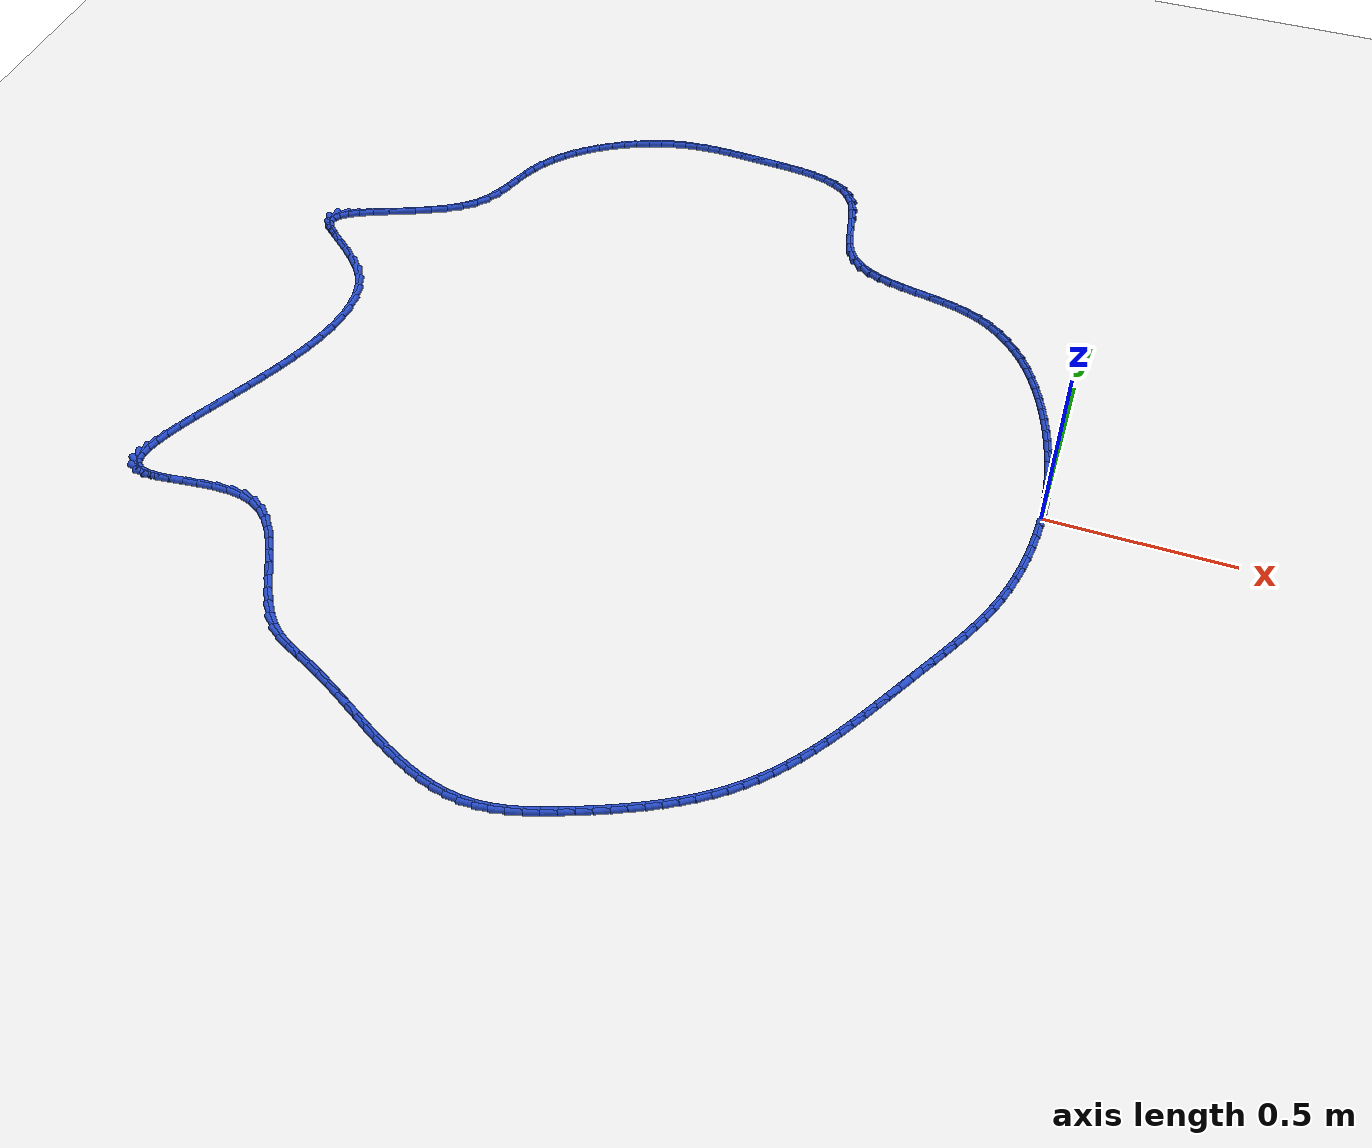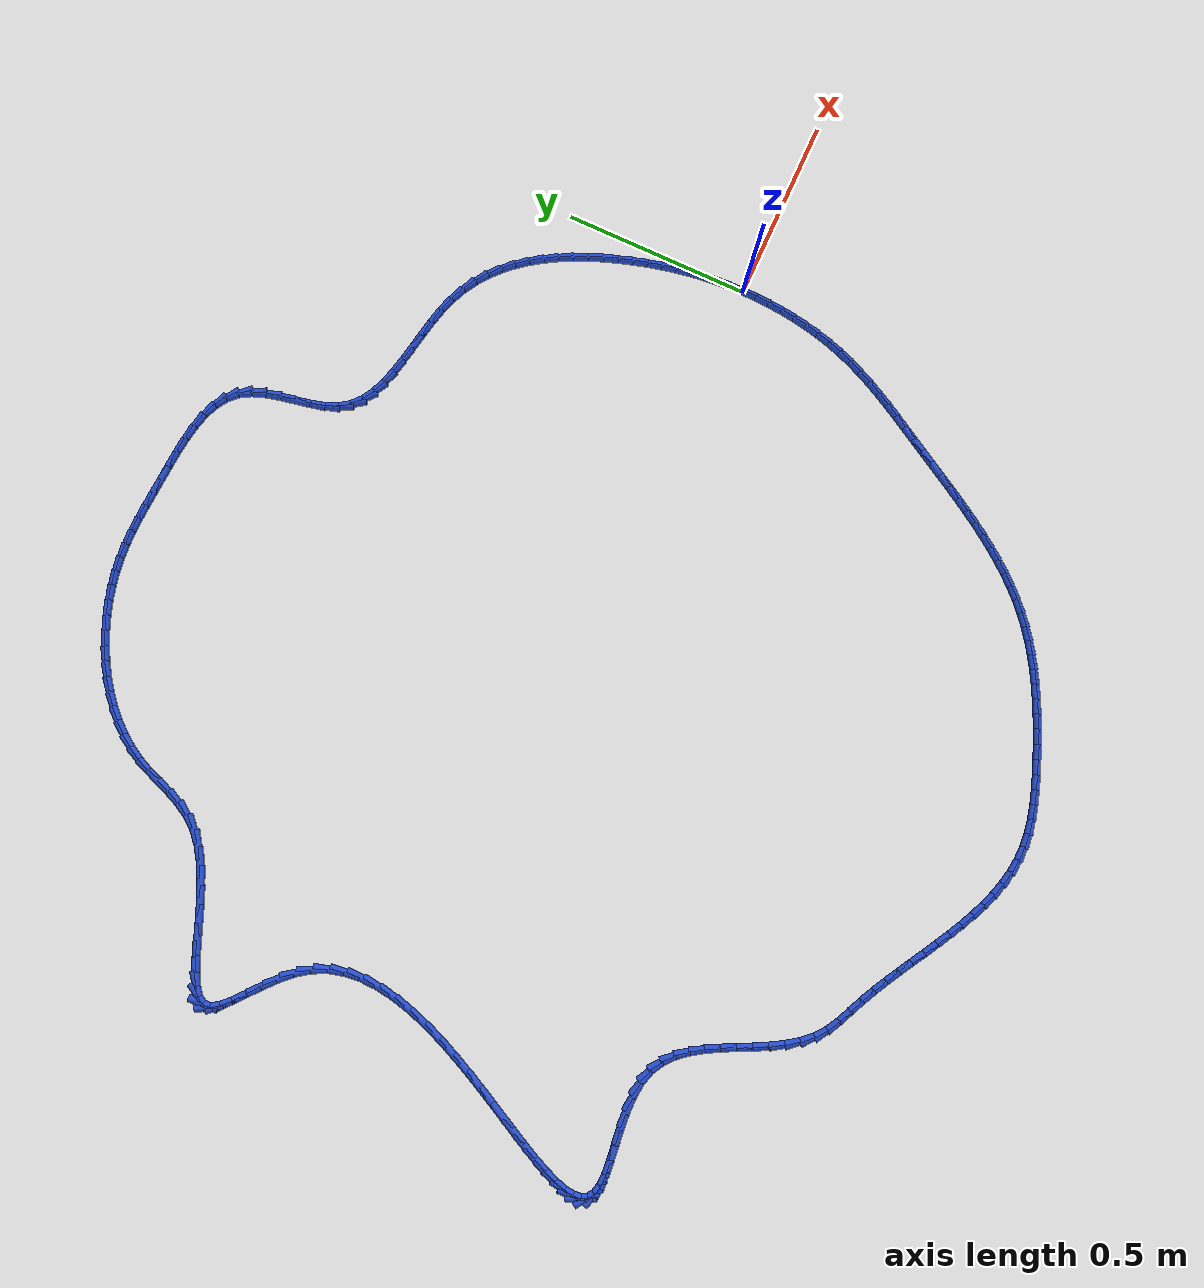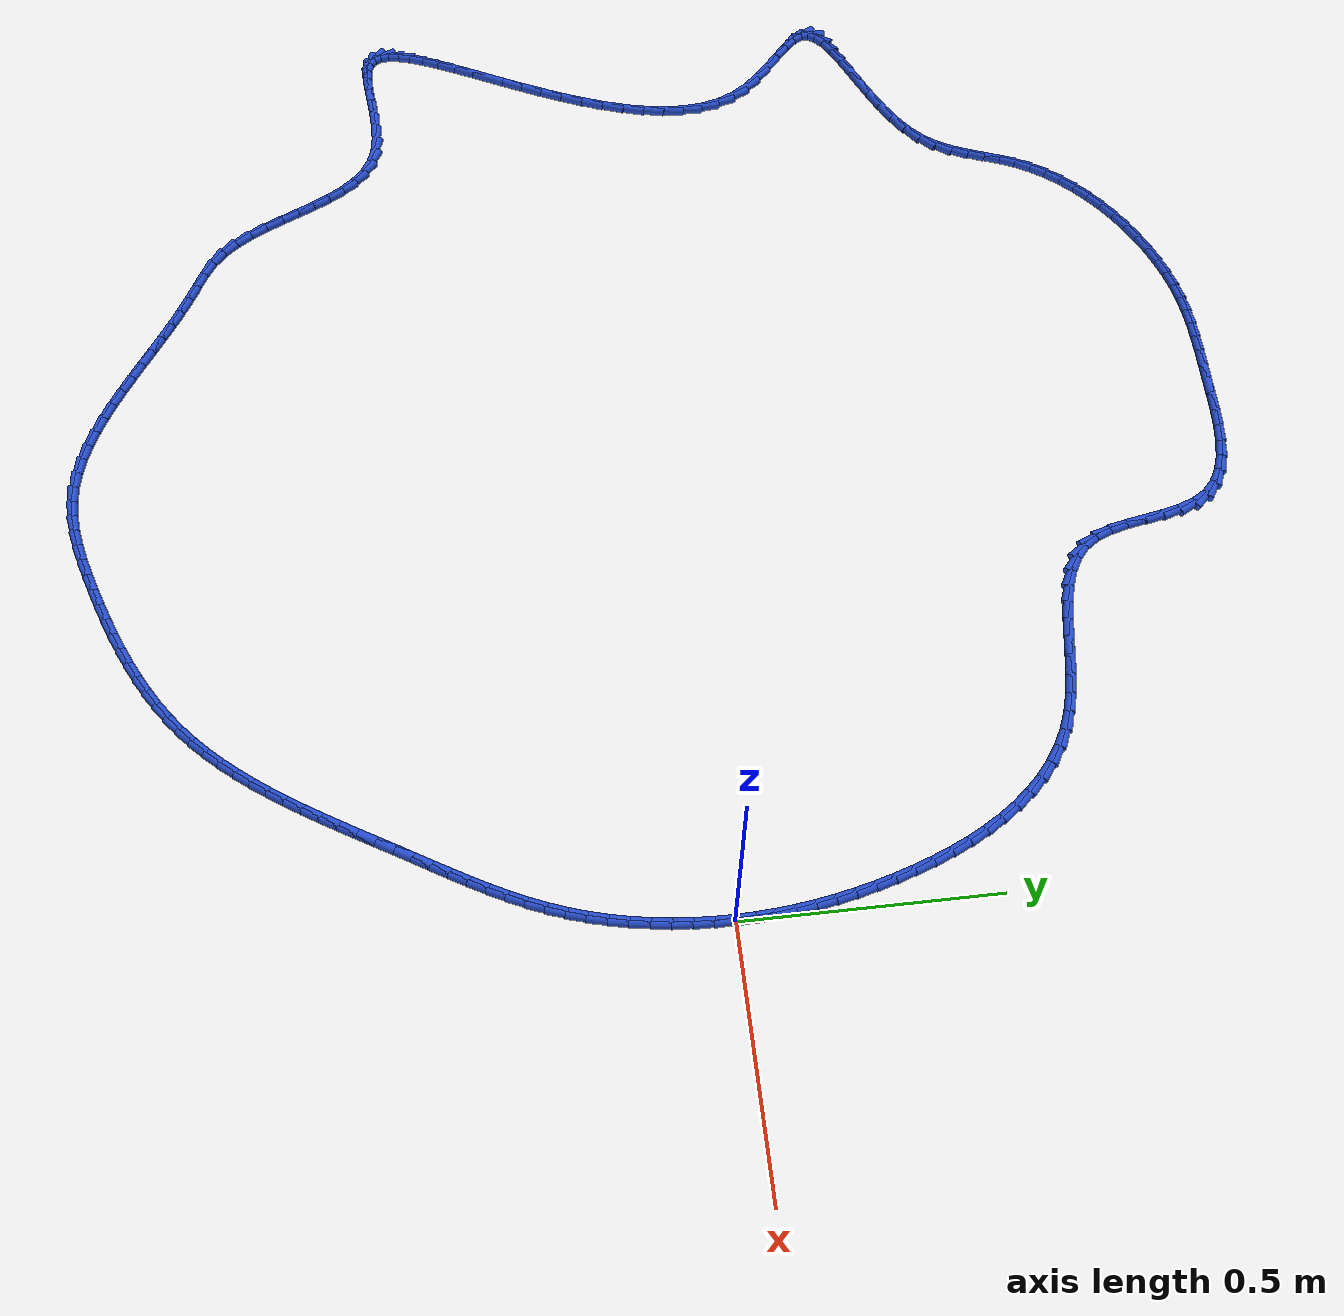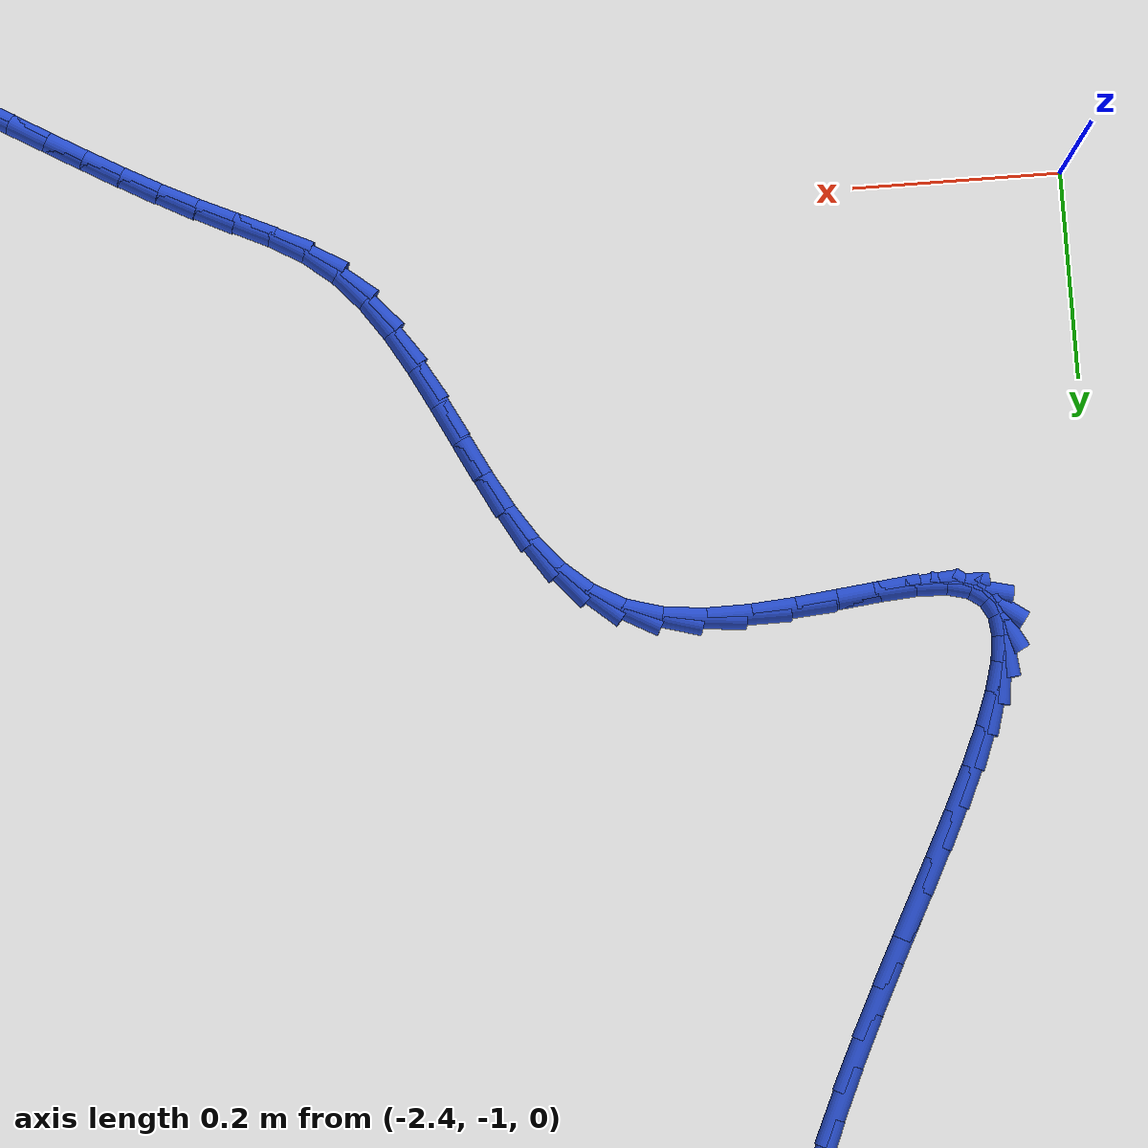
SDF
<sdf version="1.6">
 <world name="default">
  <light name="sun" type="directional">
   <pose>0 0 10 0 -0 0</pose>
   <diffuse>0.8 0.8 0.8 1</diffuse>
   <specular>0.2 0.2 0.2 1</specular>
   <attenuation>
    <range>1000</range>
    <constant>0.9</constant>
    <linear>0.01</linear>
    <quadratic>0.001</quadratic>
   </attenuation>
   <direction>-0.5 0.1 -0.9</direction>
  </light>
  <model name="ground_plane">
   <static>1</static>
   <link name="link">
    <collision name="collision">
     <geometry><plane><normal>0 0 1</normal><size>100 100</size></plane></geometry>
     <surface><friction><ode><mu>100</mu><mu2>50</mu2></ode></friction></surface>
    </collision>
    <visual name="visual">
     <cast_shadows>0</cast_shadows>
     <geometry><plane><normal>0 0 1</normal><size>100 100</size></plane></geometry>
     <material>
      <script><uri>file://media/materials/scripts/gazebo.material</uri><name>Gazebo/WhiteGlow</name></script>
     </material>
    </visual>
   </link>
  </model>
  <gravity>0 0 -9.8</gravity>
  <magnetic_field>6e-06 2.3e-05 -4.2e-05</magnetic_field>
  <atmosphere type="adiabatic"/>
  <physics name="default_physics" default="0" type="ode">
   <max_step_size>0.001</max_step_size>
   <real_time_factor>1</real_time_factor>
   <real_time_update_rate>1000</real_time_update_rate>
  </physics>
  <scene><ambient>0.4 0.4 0.4 1</ambient><background>0.7 0.7 0.7 1</background><shadows>1</shadows></scene>
  <spherical_coordinates>
   <surface_model>EARTH_WGS84</surface_model>
   <latitude_deg>0</latitude_deg>
   <longitude_deg>0</longitude_deg>
   <elevation>0</elevation>
   <heading_deg>0</heading_deg>
  </spherical_coordinates>
  <model name="line">
   <link name="link_0">
    <pose>-3.469446951953614e-18 -1.3877787807814457e-17 0.01 0 1.57 -1.5446074560020244</pose>
    <collision name="collision">
     <geometry><cylinder><radius>0.01</radius><length>0.08</length></cylinder></geometry>
    </collision>
    <visual name="visual">
     <material>
      <script><name>Gazebo/Blue</name><uri>file://media/materials/scripts/gazebo.material</uri></script>
     </material>
     <geometry><cylinder><radius>0.01</radius><length>0.08</length></cylinder></geometry>
    </visual>
   </link>
   <link name="link_1">
    <pose>-0.0009925449880114148 0.03789083045452328 0.01 0 1.57 -1.5075537437832334</pose>
    <collision name="collision">
     <geometry><cylinder><radius>0.01</radius><length>0.08</length></cylinder></geometry>
    </collision>
    <visual name="visual">
     <material>
      <script><name>Gazebo/Blue</name><uri>file://media/materials/scripts/gazebo.material</uri></script>
     </material>
     <geometry><cylinder><radius>0.01</radius><length>0.08</length></cylinder></geometry>
    </visual>
   </link>
   <link name="link_2">
    <pose>-0.003380186408068941 0.07559418212864366 0.01 0 1.57 -1.4707269061510995</pose>
    <collision name="collision">
     <geometry><cylinder><radius>0.01</radius><length>0.08</length></cylinder></geometry>
    </collision>
    <visual name="visual">
     <material>
      <script><name>Gazebo/Blue</name><uri>file://media/materials/scripts/gazebo.material</uri></script>
     </material>
     <geometry><cylinder><radius>0.01</radius><length>0.08</length></cylinder></geometry>
    </visual>
   </link>
   <link name="link_3">
    <pose>-0.007151604039434886 0.11315630992442813 0.01 0 1.57 -1.4343590799724768</pose>
    <collision name="collision">
     <geometry><cylinder><radius>0.01</radius><length>0.08</length></cylinder></geometry>
    </collision>
    <visual name="visual">
     <material>
      <script><name>Gazebo/Blue</name><uri>file://media/materials/scripts/gazebo.material</uri></script>
     </material>
     <geometry><cylinder><radius>0.01</radius><length>0.08</length></cylinder></geometry>
    </visual>
   </link>
   <link name="link_4">
    <pose>-0.012295477661371568 0.15062346874394392 0.01 0 1.57 -1.3986715624035229</pose>
    <collision name="collision">
     <geometry><cylinder><radius>0.01</radius><length>0.08</length></cylinder></geometry>
    </collision>
    <visual name="visual">
     <material>
      <script><name>Gazebo/Blue</name><uri>file://media/materials/scripts/gazebo.material</uri></script>
     </material>
     <geometry><cylinder><radius>0.01</radius><length>0.08</length></cylinder></geometry>
    </visual>
   </link>
   <link name="link_5">
    <pose>-0.018800487053141284 0.18804191348925803 0.01 0 1.57 -1.363868947554436</pose>
    <collision name="collision">
     <geometry><cylinder><radius>0.01</radius><length>0.08</length></cylinder></geometry>
    </collision>
    <visual name="visual">
     <material>
      <script><name>Gazebo/Blue</name><uri>file://media/materials/scripts/gazebo.material</uri></script>
     </material>
     <geometry><cylinder><radius>0.01</radius><length>0.08</length></cylinder></geometry>
    </visual>
   </link>
   <link name="link_6">
    <pose>-0.026655311994006357 0.22545789906243777 0.01 0 1.57 -1.3301343674706478</pose>
    <collision name="collision">
     <geometry><cylinder><radius>0.01</radius><length>0.08</length></cylinder></geometry>
    </collision>
    <visual name="visual">
     <material>
      <script><name>Gazebo/Blue</name><uri>file://media/materials/scripts/gazebo.material</uri></script>
     </material>
     <geometry><cylinder><radius>0.01</radius><length>0.08</length></cylinder></geometry>
    </visual>
   </link>
   <link name="link_7">
    <pose>-0.035848632263229104 0.26291768036555013 0.01 0 1.57 -1.297626064435137</pose>
    <collision name="collision">
     <geometry><cylinder><radius>0.01</radius><length>0.08</length></cylinder></geometry>
    </collision>
    <visual name="visual">
     <material>
      <script><name>Gazebo/Blue</name><uri>file://media/materials/scripts/gazebo.material</uri></script>
     </material>
     <geometry><cylinder><radius>0.01</radius><length>0.08</length></cylinder></geometry>
    </visual>
   </link>
   <link name="link_8">
    <pose>-0.04636912764007181 0.3004675123006622 0.01 0 1.57 -1.2660317103342464</pose>
    <collision name="collision">
     <geometry><cylinder><radius>0.01</radius><length>0.08</length></cylinder></geometry>
    </collision>
    <visual name="visual">
     <material>
      <script><name>Gazebo/Blue</name><uri>file://media/materials/scripts/gazebo.material</uri></script>
     </material>
     <geometry><cylinder><radius>0.01</radius><length>0.08</length></cylinder></geometry>
    </visual>
   </link>
   <link name="link_9">
    <pose>-0.058215243698246634 0.338126290825912 0.01 0 1.57 -1.2317283287065706</pose>
    <collision name="collision">
     <geometry><cylinder><radius>0.01</radius><length>0.08</length></cylinder></geometry>
    </collision>
    <visual name="visual">
     <material>
      <script><name>Gazebo/Blue</name><uri>file://media/materials/scripts/gazebo.material</uri></script>
     </material>
     <geometry><cylinder><radius>0.01</radius><length>0.08</length></cylinder></geometry>
    </visual>
   </link>
   <link name="link_10">
    <pose>-0.07146426075824902 0.3756920557849671 0.01 0 1.57 -1.1925718208648208</pose>
    <collision name="collision">
     <geometry><cylinder><radius>0.01</radius><length>0.08</length></cylinder></geometry>
    </collision>
    <visual name="visual">
     <material>
      <script><name>Gazebo/Blue</name><uri>file://media/materials/scripts/gazebo.material</uri></script>
     </material>
     <geometry><cylinder><radius>0.01</radius><length>0.08</length></cylinder></geometry>
    </visual>
   </link>
   <link name="link_11">
    <pose>-0.08623157831619478 0.4128560558747242 0.01 0 1.57 -1.1479991837405814</pose>
    <collision name="collision">
     <geometry><cylinder><radius>0.01</radius><length>0.08</length></cylinder></geometry>
    </collision>
    <visual name="visual">
     <material>
      <script><name>Gazebo/Blue</name><uri>file://media/materials/scripts/gazebo.material</uri></script>
     </material>
     <geometry><cylinder><radius>0.01</radius><length>0.08</length></cylinder></geometry>
    </visual>
   </link>
   <link name="link_12">
    <pose>-0.10263284412014943 0.4493088443124439 0.01 0 1.57 -1.097379973854629</pose>
    <collision name="collision">
     <geometry><cylinder><radius>0.01</radius><length>0.08</length></cylinder></geometry>
    </collision>
    <visual name="visual">
     <material>
      <script><name>Gazebo/Blue</name><uri>file://media/materials/scripts/gazebo.material</uri></script>
     </material>
     <geometry><cylinder><radius>0.01</radius><length>0.08</length></cylinder></geometry>
    </visual>
   </link>
   <link name="link_13">
    <pose>-0.12078370591817847 0.48474097431538726 0.01 0 1.57 -1.0400293793883233</pose>
    <collision name="collision">
     <geometry><cylinder><radius>0.01</radius><length>0.08</length></cylinder></geometry>
    </collision>
    <visual name="visual">
     <material>
      <script><name>Gazebo/Blue</name><uri>file://media/materials/scripts/gazebo.material</uri></script>
     </material>
     <geometry><cylinder><radius>0.01</radius><length>0.08</length></cylinder></geometry>
    </visual>
   </link>
   <link name="link_14">
    <pose>-0.1407998114583474 0.5188429991008149 0.01 0 1.57 -0.97525365627535</pose>
    <collision name="collision">
     <geometry><cylinder><radius>0.01</radius><length>0.08</length></cylinder></geometry>
    </collision>
    <visual name="visual">
     <material>
      <script><name>Gazebo/Blue</name><uri>file://media/materials/scripts/gazebo.material</uri></script>
     </material>
     <geometry><cylinder><radius>0.01</radius><length>0.08</length></cylinder></geometry>
    </visual>
   </link>
   <link name="link_15">
    <pose>-0.16279680848872158 0.551305471885987 0.01 0 1.57 -0.902427134974382</pose>
    <collision name="collision">
     <geometry><cylinder><radius>0.01</radius><length>0.08</length></cylinder></geometry>
    </collision>
    <visual name="visual">
     <material>
      <script><name>Gazebo/Blue</name><uri>file://media/materials/scripts/gazebo.material</uri></script>
     </material>
     <geometry><cylinder><radius>0.01</radius><length>0.08</length></cylinder></geometry>
    </visual>
   </link>
   <link name="link_16">
    <pose>-0.18689034475736666 0.5818189458881652 0.01 0 1.57 -0.8211102158897862</pose>
    <collision name="collision">
     <geometry><cylinder><radius>0.01</radius><length>0.08</length></cylinder></geometry>
    </collision>
    <visual name="visual">
     <material>
      <script><name>Gazebo/Blue</name><uri>file://media/materials/scripts/gazebo.material</uri></script>
     </material>
     <geometry><cylinder><radius>0.01</radius><length>0.08</length></cylinder></geometry>
    </visual>
   </link>
   <link name="link_17">
    <pose>-0.21319606801234806 0.6100739743246096 0.01 0 1.57 -0.7312100225144185</pose>
    <collision name="collision">
     <geometry><cylinder><radius>0.01</radius><length>0.08</length></cylinder></geometry>
    </collision>
    <visual name="visual">
     <material>
      <script><name>Gazebo/Blue</name><uri>file://media/materials/scripts/gazebo.material</uri></script>
     </material>
     <geometry><cylinder><radius>0.01</radius><length>0.08</length></cylinder></geometry>
    </visual>
   </link>
   <link name="link_18">
    <pose>-0.24182962600173127 0.6357611104125811 0.01 0 1.57 -0.6331665235282508</pose>
    <collision name="collision">
     <geometry><cylinder><radius>0.01</radius><length>0.08</length></cylinder></geometry>
    </collision>
    <visual name="visual">
     <material>
      <script><name>Gazebo/Blue</name><uri>file://media/materials/scripts/gazebo.material</uri></script>
     </material>
     <geometry><cylinder><radius>0.01</radius><length>0.08</length></cylinder></geometry>
    </visual>
   </link>
   <link name="link_19">
    <pose>-0.27290666647358175 0.6585709073693404 0.01 0 1.57 -0.5281168473240714</pose>
    <collision name="collision">
     <geometry><cylinder><radius>0.01</radius><length>0.08</length></cylinder></geometry>
    </collision>
    <visual name="visual">
     <material>
      <script><name>Gazebo/Blue</name><uri>file://media/materials/scripts/gazebo.material</uri></script>
     </material>
     <geometry><cylinder><radius>0.01</radius><length>0.08</length></cylinder></geometry>
    </visual>
   </link>
   <link name="link_20">
    <pose>-0.3065428371759651 0.6781939184121484 0.01 0 1.57 -0.41812735835088943</pose>
    <collision name="collision">
     <geometry><cylinder><radius>0.01</radius><length>0.08</length></cylinder></geometry>
    </collision>
    <visual name="visual">
     <material>
      <script><name>Gazebo/Blue</name><uri>file://media/materials/scripts/gazebo.material</uri></script>
     </material>
     <geometry><cylinder><radius>0.01</radius><length>0.08</length></cylinder></geometry>
    </visual>
   </link>
   <link name="link_21">
    <pose>-0.3428496800243628 0.694326077023281 0.01 0 1.57 -0.317876370933119</pose>
    <collision name="collision">
     <geometry><cylinder><radius>0.01</radius><length>0.08</length></cylinder></geometry>
    </collision>
    <visual name="visual">
     <material>
      <script><name>Gazebo/Blue</name><uri>file://media/materials/scripts/gazebo.material</uri></script>
     </material>
     <geometry><cylinder><radius>0.01</radius><length>0.08</length></cylinder></geometry>
    </visual>
   </link>
   <link name="link_22">
    <pose>-0.381618871149801 0.7070824674064984 0.01 0 1.57 -0.2470209636867362</pose>
    <collision name="collision">
     <geometry><cylinder><radius>0.01</radius><length>0.08</length></cylinder></geometry>
    </collision>
    <visual name="visual">
     <material>
      <script><name>Gazebo/Blue</name><uri>file://media/materials/scripts/gazebo.material</uri></script>
     </material>
     <geometry><cylinder><radius>0.01</radius><length>0.08</length></cylinder></geometry>
    </visual>
   </link>
   <link name="link_23">
    <pose>-0.42209864669319136 0.7172902951458662 0.01 0 1.57 -0.20385755645582793</pose>
    <collision name="collision">
     <geometry><cylinder><radius>0.01</radius><length>0.08</length></cylinder></geometry>
    </collision>
    <visual name="visual">
     <material>
      <script><name>Gazebo/Blue</name><uri>file://media/materials/scripts/gazebo.material</uri></script>
     </material>
     <geometry><cylinder><radius>0.01</radius><length>0.08</length></cylinder></geometry>
    </visual>
   </link>
   <link name="link_24">
    <pose>-0.46348444561271684 0.7258459510222056 0.01 0 1.57 -0.18583720344513216</pose>
    <collision name="collision">
     <geometry><cylinder><radius>0.01</radius><length>0.08</length></cylinder></geometry>
    </collision>
    <visual name="visual">
     <material>
      <script><name>Gazebo/Blue</name><uri>file://media/materials/scripts/gazebo.material</uri></script>
     </material>
     <geometry><cylinder><radius>0.01</radius><length>0.08</length></cylinder></geometry>
    </visual>
   </link>
   <link name="link_25">
    <pose>-0.5049717068665608 0.7336458258163382 0.01 0 1.57 -0.1922897160899658</pose>
    <collision name="collision">
     <geometry><cylinder><radius>0.01</radius><length>0.08</length></cylinder></geometry>
    </collision>
    <visual name="visual">
     <material>
      <script><name>Gazebo/Blue</name><uri>file://media/materials/scripts/gazebo.material</uri></script>
     </material>
     <geometry><cylinder><radius>0.01</radius><length>0.08</length></cylinder></geometry>
    </visual>
   </link>
   <link name="link_26">
    <pose>-0.5457558694129059 0.7415863103090854 0.01 0 1.57 -0.22471113498920764</pose>
    <collision name="collision">
     <geometry><cylinder><radius>0.01</radius><length>0.08</length></cylinder></geometry>
    </collision>
    <visual name="visual">
     <material>
      <script><name>Gazebo/Blue</name><uri>file://media/materials/scripts/gazebo.material</uri></script>
     </material>
     <geometry><cylinder><radius>0.01</radius><length>0.08</length></cylinder></geometry>
    </visual>
   </link>
   <link name="link_27">
    <pose>-0.5850323722099358 0.7505637952812692 0.01 0 1.57 -0.2870229454255299</pose>
    <collision name="collision">
     <geometry><cylinder><radius>0.01</radius><length>0.08</length></cylinder></geometry>
    </collision>
    <visual name="visual">
     <material>
      <script><name>Gazebo/Blue</name><uri>file://media/materials/scripts/gazebo.material</uri></script>
     </material>
     <geometry><cylinder><radius>0.01</radius><length>0.08</length></cylinder></geometry>
    </visual>
   </link>
   <link name="link_28">
    <pose>-0.621996654215833 0.7614746715137105 0.01 0 1.57 -0.38563187657112863</pose>
    <collision name="collision">
     <geometry><cylinder><radius>0.01</radius><length>0.08</length></cylinder></geometry>
    </collision>
    <visual name="visual">
     <material>
      <script><name>Gazebo/Blue</name><uri>file://media/materials/scripts/gazebo.material</uri></script>
     </material>
     <geometry><cylinder><radius>0.01</radius><length>0.08</length></cylinder></geometry>
    </visual>
   </link>
   <link name="link_29">
    <pose>-0.6558441543887806 0.775215329787231 0.01 0 1.57 -0.5283213877139848</pose>
    <collision name="collision">
     <geometry><cylinder><radius>0.01</radius><length>0.08</length></cylinder></geometry>
    </collision>
    <visual name="visual">
     <material>
      <script><name>Gazebo/Blue</name><uri>file://media/materials/scripts/gazebo.material</uri></script>
     </material>
     <geometry><cylinder><radius>0.01</radius><length>0.08</length></cylinder></geometry>
    </visual>
   </link>
   <link name="link_30">
    <pose>-0.6857703116869618 0.7926821608826521 0.01 0 1.57 -0.7197097283849764</pose>
    <collision name="collision">
     <geometry><cylinder><radius>0.01</radius><length>0.08</length></cylinder></geometry>
    </collision>
    <visual name="visual">
     <material>
      <script><name>Gazebo/Blue</name><uri>file://media/materials/scripts/gazebo.material</uri></script>
     </material>
     <geometry><cylinder><radius>0.01</radius><length>0.08</length></cylinder></geometry>
    </visual>
   </link>
   <link name="link_31">
    <pose>-0.7109705650685599 0.8147715555807955 0.01 0 1.57 -0.9515350499302929</pose>
    <collision name="collision">
     <geometry><cylinder><radius>0.01</radius><length>0.08</length></cylinder></geometry>
    </collision>
    <visual name="visual">
     <material>
      <script><name>Gazebo/Blue</name><uri>file://media/materials/scripts/gazebo.material</uri></script>
     </material>
     <geometry><cylinder><radius>0.01</radius><length>0.08</length></cylinder></geometry>
    </visual>
   </link>
   <link name="link_32">
    <pose>-0.7306457235936005 0.8423744090537564 0.01 0 1.57 -1.168081435696967</pose>
    <collision name="collision">
     <geometry><cylinder><radius>0.01</radius><length>0.08</length></cylinder></geometry>
    </collision>
    <visual name="visual">
     <material>
      <script><name>Gazebo/Blue</name><uri>file://media/materials/scripts/gazebo.material</uri></script>
     </material>
     <geometry><cylinder><radius>0.01</radius><length>0.08</length></cylinder></geometry>
    </visual>
   </link>
   <link name="link_33">
    <pose>-0.7447877772190492 0.8755719445588925 0.01 0 1.57 -1.3027888521186535</pose>
    <collision name="collision">
     <geometry><cylinder><radius>0.01</radius><length>0.08</length></cylinder></geometry>
    </collision>
    <visual name="visual">
     <material>
      <script><name>Gazebo/Blue</name><uri>file://media/materials/scripts/gazebo.material</uri></script>
     </material>
     <geometry><cylinder><radius>0.01</radius><length>0.08</length></cylinder></geometry>
    </visual>
   </link>
   <link name="link_34">
    <pose>-0.755007924955348 0.9127883330918626 0.01 0 1.57 -1.3681372646120227</pose>
    <collision name="collision">
     <geometry><cylinder><radius>0.01</radius><length>0.08</length></cylinder></geometry>
    </collision>
    <visual name="visual">
     <material>
      <script><name>Gazebo/Blue</name><uri>file://media/materials/scripts/gazebo.material</uri></script>
     </material>
     <geometry><cylinder><radius>0.01</radius><length>0.08</length></cylinder></geometry>
    </visual>
   </link>
   <link name="link_35">
    <pose>-0.7631154764235458 0.9522450049122431 0.01 0 1.57 -1.3777260906660382</pose>
    <collision name="collision">
     <geometry><cylinder><radius>0.01</radius><length>0.08</length></cylinder></geometry>
    </collision>
    <visual name="visual">
     <material>
      <script><name>Gazebo/Blue</name><uri>file://media/materials/scripts/gazebo.material</uri></script>
     </material>
     <geometry><cylinder><radius>0.01</radius><length>0.08</length></cylinder></geometry>
    </visual>
   </link>
   <link name="link_36">
    <pose>-0.7709197412446919 0.9921633902796094 0.01 0 1.57 -1.334126829078799</pose>
    <collision name="collision">
     <geometry><cylinder><radius>0.01</radius><length>0.08</length></cylinder></geometry>
    </collision>
    <visual name="visual">
     <material>
      <script><name>Gazebo/Blue</name><uri>file://media/materials/scripts/gazebo.material</uri></script>
     </material>
     <geometry><cylinder><radius>0.01</radius><length>0.08</length></cylinder></geometry>
    </visual>
   </link>
   <link name="link_37">
    <pose>-0.7802300290398345 1.030764919453538 0.01 0 1.57 -1.2291501292956815</pose>
    <collision name="collision">
     <geometry><cylinder><radius>0.01</radius><length>0.08</length></cylinder></geometry>
    </collision>
    <visual name="visual">
     <material>
      <script><name>Gazebo/Blue</name><uri>file://media/materials/scripts/gazebo.material</uri></script>
     </material>
     <geometry><cylinder><radius>0.01</radius><length>0.08</length></cylinder></geometry>
    </visual>
   </link>
   <link name="link_38">
    <pose>-0.7928556494300238 1.0662710226936056 0.01 0 1.57 -1.0456197366940465</pose>
    <collision name="collision">
     <geometry><cylinder><radius>0.01</radius><length>0.08</length></cylinder></geometry>
    </collision>
    <visual name="visual">
     <material>
      <script><name>Gazebo/Blue</name><uri>file://media/materials/scripts/gazebo.material</uri></script>
     </material>
     <geometry><cylinder><radius>0.01</radius><length>0.08</length></cylinder></geometry>
    </visual>
   </link>
   <link name="link_39">
    <pose>-0.8106057120175395 1.0969033129298695 0.01 0 1.57 -0.7941725816603435</pose>
    <collision name="collision">
     <geometry><cylinder><radius>0.01</radius><length>0.08</length></cylinder></geometry>
    </collision>
    <visual name="visual">
     <material>
      <script><name>Gazebo/Blue</name><uri>file://media/materials/scripts/gazebo.material</uri></script>
     </material>
     <geometry><cylinder><radius>0.01</radius><length>0.08</length></cylinder></geometry>
    </visual>
   </link>
   <link name="link_40">
    <pose>-0.8346986709791938 1.1214228290274817 0.01 0 1.57 -0.5655866208523501</pose>
    <collision name="collision">
     <geometry><cylinder><radius>0.01</radius><length>0.08</length></cylinder></geometry>
    </collision>
    <visual name="visual">
     <material>
      <script><name>Gazebo/Blue</name><uri>file://media/materials/scripts/gazebo.material</uri></script>
     </material>
     <geometry><cylinder><radius>0.01</radius><length>0.08</length></cylinder></geometry>
    </visual>
   </link>
   <link name="link_41">
    <pose>-0.8644634175951799 1.1403162847349129 0.01 0 1.57 -0.38907833267353564</pose>
    <collision name="collision">
     <geometry><cylinder><radius>0.01</radius><length>0.08</length></cylinder></geometry>
    </collision>
    <visual name="visual">
     <material>
      <script><name>Gazebo/Blue</name><uri>file://media/materials/scripts/gazebo.material</uri></script>
     </material>
     <geometry><cylinder><radius>0.01</radius><length>0.08</length></cylinder></geometry>
    </visual>
   </link>
   <link name="link_42">
    <pose>-0.8988517791090376 1.1544147538315281 0.01 0 1.57 -0.2608698189846857</pose>
    <collision name="collision">
     <geometry><cylinder><radius>0.01</radius><length>0.08</length></cylinder></geometry>
    </collision>
    <visual name="visual">
     <material>
      <script><name>Gazebo/Blue</name><uri>file://media/materials/scripts/gazebo.material</uri></script>
     </material>
     <geometry><cylinder><radius>0.01</radius><length>0.08</length></cylinder></geometry>
    </visual>
   </link>
   <link name="link_43">
    <pose>-0.9368155827643069 1.1645493100966922 0.01 0 1.57 -0.17122678400011776</pose>
    <collision name="collision">
     <geometry><cylinder><radius>0.01</radius><length>0.08</length></cylinder></geometry>
    </collision>
    <visual name="visual">
     <material>
      <script><name>Gazebo/Blue</name><uri>file://media/materials/scripts/gazebo.material</uri></script>
     </material>
     <geometry><cylinder><radius>0.01</radius><length>0.08</length></cylinder></geometry>
    </visual>
   </link>
   <link name="link_44">
    <pose>-0.977306655804528 1.1715510273097698 0.01 0 1.57 -0.11151854596318879</pose>
    <collision name="collision">
     <geometry><cylinder><radius>0.01</radius><length>0.08</length></cylinder></geometry>
    </collision>
    <visual name="visual">
     <material>
      <script><name>Gazebo/Blue</name><uri>file://media/materials/scripts/gazebo.material</uri></script>
     </material>
     <geometry><cylinder><radius>0.01</radius><length>0.08</length></cylinder></geometry>
    </visual>
   </link>
   <link name="link_45">
    <pose>-1.0192768254732398 1.1762509792501257 0.01 0 1.57 -0.0760130985941276</pose>
    <collision name="collision">
     <geometry><cylinder><radius>0.01</radius><length>0.08</length></cylinder></geometry>
    </collision>
    <visual name="visual">
     <material>
      <script><name>Gazebo/Blue</name><uri>file://media/materials/scripts/gazebo.material</uri></script>
     </material>
     <geometry><cylinder><radius>0.01</radius><length>0.08</length></cylinder></geometry>
    </visual>
   </link>
   <link name="link_46">
    <pose>-1.0616779190139827 1.1794802396971247 0.01 0 1.57 -0.06189795666822843</pose>
    <collision name="collision">
     <geometry><cylinder><radius>0.01</radius><length>0.08</length></cylinder></geometry>
    </collision>
    <visual name="visual">
     <material>
      <script><name>Gazebo/Blue</name><uri>file://media/materials/scripts/gazebo.material</uri></script>
     </material>
     <geometry><cylinder><radius>0.01</radius><length>0.08</length></cylinder></geometry>
    </visual>
   </link>
   <link name="link_47">
    <pose>-1.1034617636702966 1.182069882430132 0.01 0 1.57 -0.06379656134763402</pose>
    <collision name="collision">
     <geometry><cylinder><radius>0.01</radius><length>0.08</length></cylinder></geometry>
    </collision>
    <visual name="visual">
     <material>
      <script><name>Gazebo/Blue</name><uri>file://media/materials/scripts/gazebo.material</uri></script>
     </material>
     <geometry><cylinder><radius>0.01</radius><length>0.08</length></cylinder></geometry>
    </visual>
   </link>
   <link name="link_48">
    <pose>-1.1438059049551923 1.1846471974221366 0.01 0 1.57 -0.060404298847536425</pose>
    <collision name="collision">
     <geometry><cylinder><radius>0.01</radius><length>0.08</length></cylinder></geometry>
    </collision>
    <visual name="visual">
     <material>
      <script><name>Gazebo/Blue</name><uri>file://media/materials/scripts/gazebo.material</uri></script>
     </material>
     <geometry><cylinder><radius>0.01</radius><length>0.08</length></cylinder></geometry>
    </visual>
   </link>
   <link name="link_49">
    <pose>-1.1828109221812215 1.1870061378430354 0.01 0 1.57 -0.04526971642761771</pose>
    <collision name="collision">
     <geometry><cylinder><radius>0.01</radius><length>0.08</length></cylinder></geometry>
    </collision>
    <visual name="visual">
     <material>
      <script><name>Gazebo/Blue</name><uri>file://media/materials/scripts/gazebo.material</uri></script>
     </material>
     <geometry><cylinder><radius>0.01</radius><length>0.08</length></cylinder></geometry>
    </visual>
   </link>
   <link name="link_50">
    <pose>-1.2208133053272079 1.1887276711188097 0.01 0 1.57 -0.01781173337337017</pose>
    <collision name="collision">
     <geometry><cylinder><radius>0.01</radius><length>0.08</length></cylinder></geometry>
    </collision>
    <visual name="visual">
     <material>
      <script><name>Gazebo/Blue</name><uri>file://media/materials/scripts/gazebo.material</uri></script>
     </material>
     <geometry><cylinder><radius>0.01</radius><length>0.08</length></cylinder></geometry>
    </visual>
   </link>
   <link name="link_51">
    <pose>-1.2581495444640256 1.189392764592341 0.01 0 1.57 0.021894738039404168</pose>
    <collision name="collision">
     <geometry><cylinder><radius>0.01</radius><length>0.08</length></cylinder></geometry>
    </collision>
    <visual name="visual">
     <material>
      <script><name>Gazebo/Blue</name><uri>file://media/materials/scripts/gazebo.material</uri></script>
     </material>
     <geometry><cylinder><radius>0.01</radius><length>0.08</length></cylinder></geometry>
    </visual>
   </link>
   <link name="link_52">
    <pose>-1.2951561296625478 1.188582385606509 0.01 0 1.57 0.07294879168000383</pose>
    <collision name="collision">
     <geometry><cylinder><radius>0.01</radius><length>0.08</length></cylinder></geometry>
    </collision>
    <visual name="visual">
     <material>
      <script><name>Gazebo/Blue</name><uri>file://media/materials/scripts/gazebo.material</uri></script>
     </material>
     <geometry><cylinder><radius>0.01</radius><length>0.08</length></cylinder></geometry>
    </visual>
   </link>
   <link name="link_53">
    <pose>-1.3321695509936469 1.1858775015041942 0.01 0 1.57 0.13348053454037398</pose>
    <collision name="collision">
     <geometry><cylinder><radius>0.01</radius><length>0.08</length></cylinder></geometry>
    </collision>
    <visual name="visual">
     <material>
      <script><name>Gazebo/Blue</name><uri>file://media/materials/scripts/gazebo.material</uri></script>
     </material>
     <geometry><cylinder><radius>0.01</radius><length>0.08</length></cylinder></geometry>
    </visual>
   </link>
   <link name="link_54">
    <pose>-1.3695227634542462 1.1808617506619292 0.01 0 1.57 0.1975852612919614</pose>
    <collision name="collision">
     <geometry><cylinder><radius>0.01</radius><length>0.08</length></cylinder></geometry>
    </collision>
    <visual name="visual">
     <material>
      <script><name>Gazebo/Blue</name><uri>file://media/materials/scripts/gazebo.material</uri></script>
     </material>
     <geometry><cylinder><radius>0.01</radius><length>0.08</length></cylinder></geometry>
    </visual>
   </link>
   <link name="link_55">
    <pose>-1.4073141362033281 1.1732960199881108 0.01 0 1.57 0.2593633638414282</pose>
    <collision name="collision">
     <geometry><cylinder><radius>0.01</radius><length>0.08</length></cylinder></geometry>
    </collision>
    <visual name="visual">
     <material>
      <script><name>Gazebo/Blue</name><uri>file://media/materials/scripts/gazebo.material</uri></script>
     </material>
     <geometry><cylinder><radius>0.01</radius><length>0.08</length></cylinder></geometry>
    </visual>
   </link>
   <link name="link_56">
    <pose>-1.4452648782610118 1.1632261713132244 0.01 0 1.57 0.319445621223267</pose>
    <collision name="collision">
     <geometry><cylinder><radius>0.01</radius><length>0.08</length></cylinder></geometry>
    </collision>
    <visual name="visual">
     <material>
      <script><name>Gazebo/Blue</name><uri>file://media/materials/scripts/gazebo.material</uri></script>
     </material>
     <geometry><cylinder><radius>0.01</radius><length>0.08</length></cylinder></geometry>
    </visual>
   </link>
   <link name="link_57">
    <pose>-1.483062117451954 1.1507238175613121 0.01 0 1.57 0.3789096621562624</pose>
    <collision name="collision">
     <geometry><cylinder><radius>0.01</radius><length>0.08</length></cylinder></geometry>
    </collision>
    <visual name="visual">
     <material>
      <script><name>Gazebo/Blue</name><uri>file://media/materials/scripts/gazebo.material</uri></script>
     </material>
     <geometry><cylinder><radius>0.01</radius><length>0.08</length></cylinder></geometry>
    </visual>
   </link>
   <link name="link_58">
    <pose>-1.5203929816008117 1.135860571656416 0.01 0 1.57 0.43876163059454654</pose>
    <collision name="collision">
     <geometry><cylinder><radius>0.01</radius><length>0.08</length></cylinder></geometry>
    </collision>
    <visual name="visual">
     <material>
      <script><name>Gazebo/Blue</name><uri>file://media/materials/scripts/gazebo.material</uri></script>
     </material>
     <geometry><cylinder><radius>0.01</radius><length>0.08</length></cylinder></geometry>
    </visual>
   </link>
   <link name="link_59">
    <pose>-1.556944598532242 1.1187080465225778 0.01 0 1.57 0.4999691505312151</pose>
    <collision name="collision">
     <geometry><cylinder><radius>0.01</radius><length>0.08</length></cylinder></geometry>
    </collision>
    <visual name="visual">
     <material>
      <script><name>Gazebo/Blue</name><uri>file://media/materials/scripts/gazebo.material</uri></script>
     </material>
     <geometry><cylinder><radius>0.01</radius><length>0.08</length></cylinder></geometry>
    </visual>
   </link>
   <link name="link_60">
    <pose>-1.5924040960709023 1.0993378550838402 0.01 0 1.57 0.5634870245357481</pose>
    <collision name="collision">
     <geometry><cylinder><radius>0.01</radius><length>0.08</length></cylinder></geometry>
    </collision>
    <visual name="visual">
     <material>
      <script><name>Gazebo/Blue</name><uri>file://media/materials/scripts/gazebo.material</uri></script>
     </material>
     <geometry><cylinder><radius>0.01</radius><length>0.08</length></cylinder></geometry>
    </visual>
   </link>
   <link name="link_61">
    <pose>-1.6264586020414489 1.0778216102642444 0.01 0 1.57 0.6302737982823637</pose>
    <collision name="collision">
     <geometry><cylinder><radius>0.01</radius><length>0.08</length></cylinder></geometry>
    </collision>
    <visual name="visual">
     <material>
      <script><name>Gazebo/Blue</name><uri>file://media/materials/scripts/gazebo.material</uri></script>
     </material>
     <geometry><cylinder><radius>0.01</radius><length>0.08</length></cylinder></geometry>
    </visual>
   </link>
   <link name="link_62">
    <pose>-1.6587952442685392 1.0542309249878328 0.01 0 1.57 0.701295721354656</pose>
    <collision name="collision">
     <geometry><cylinder><radius>0.01</radius><length>0.08</length></cylinder></geometry>
    </collision>
    <visual name="visual">
     <material>
      <script><name>Gazebo/Blue</name><uri>file://media/materials/scripts/gazebo.material</uri></script>
     </material>
     <geometry><cylinder><radius>0.01</radius><length>0.08</length></cylinder></geometry>
    </visual>
   </link>
   <link name="link_63">
    <pose>-1.6891011505768299 1.0286374121786475 0.01 0 1.57 0.7775123248453703</pose>
    <collision name="collision">
     <geometry><cylinder><radius>0.01</radius><length>0.08</length></cylinder></geometry>
    </collision>
    <visual name="visual">
     <material>
      <script><name>Gazebo/Blue</name><uri>file://media/materials/scripts/gazebo.material</uri></script>
     </material>
     <geometry><cylinder><radius>0.01</radius><length>0.08</length></cylinder></geometry>
    </visual>
   </link>
   <link name="link_64">
    <pose>-1.7170634487909786 1.0011126847607306 0.01 0 1.57 0.85983525573951</pose>
    <collision name="collision">
     <geometry><cylinder><radius>0.01</radius><length>0.08</length></cylinder></geometry>
    </collision>
    <visual name="visual">
     <material>
      <script><name>Gazebo/Blue</name><uri>file://media/materials/scripts/gazebo.material</uri></script>
     </material>
     <geometry><cylinder><radius>0.01</radius><length>0.08</length></cylinder></geometry>
    </visual>
   </link>
   <link name="link_65">
    <pose>-1.7423692667356414 0.9717283556581238 0.01 0 1.57 0.9490503693211537</pose>
    <collision name="collision">
     <geometry><cylinder><radius>0.01</radius><length>0.08</length></cylinder></geometry>
    </collision>
    <visual name="visual">
     <material>
      <script><name>Gazebo/Blue</name><uri>file://media/materials/scripts/gazebo.material</uri></script>
     </material>
     <geometry><cylinder><radius>0.01</radius><length>0.08</length></cylinder></geometry>
    </visual>
   </link>
   <link name="link_66">
    <pose>-1.7647057322354762 0.9405560377948695 0.01 0 1.57 1.0456950409945203</pose>
    <collision name="collision">
     <geometry><cylinder><radius>0.01</radius><length>0.08</length></cylinder></geometry>
    </collision>
    <visual name="visual">
     <material>
      <script><name>Gazebo/Blue</name><uri>file://media/materials/scripts/gazebo.material</uri></script>
     </material>
     <geometry><cylinder><radius>0.01</radius><length>0.08</length></cylinder></geometry>
    </visual>
   </link>
   <link name="link_67">
    <pose>-1.783759973115139 0.9076673440950094 0.01 0 1.57 1.1435086841225959</pose>
    <collision name="collision">
     <geometry><cylinder><radius>0.01</radius><length>0.08</length></cylinder></geometry>
    </collision>
    <visual name="visual">
     <material>
      <script><name>Gazebo/Blue</name><uri>file://media/materials/scripts/gazebo.material</uri></script>
     </material>
     <geometry><cylinder><radius>0.01</radius><length>0.08</length></cylinder></geometry>
    </visual>
   </link>
   <link name="link_68">
    <pose>-1.799448794484213 0.873212334070367 0.01 0 1.57 1.2024026393650187</pose>
    <collision name="collision">
     <geometry><cylinder><radius>0.01</radius><length>0.08</length></cylinder></geometry>
    </collision>
    <visual name="visual">
     <material>
      <script><name>Gazebo/Blue</name><uri>file://media/materials/scripts/gazebo.material</uri></script>
     </material>
     <geometry><cylinder><radius>0.01</radius><length>0.08</length></cylinder></geometry>
    </visual>
   </link>
   <link name="link_69">
    <pose>-1.8131085326556455 0.8378259100381336 0.01 0 1.57 1.207169072288135</pose>
    <collision name="collision">
     <geometry><cylinder><radius>0.01</radius><length>0.08</length></cylinder></geometry>
    </collision>
    <visual name="visual">
     <material>
      <script><name>Gazebo/Blue</name><uri>file://media/materials/scripts/gazebo.material</uri></script>
     </material>
     <geometry><cylinder><radius>0.01</radius><length>0.08</length></cylinder></geometry>
    </visual>
   </link>
   <link name="link_70">
    <pose>-1.8266172507014728 0.8023280018238768 0.01 0 1.57 1.1579852641284027</pose>
    <collision name="collision">
     <geometry><cylinder><radius>0.01</radius><length>0.08</length></cylinder></geometry>
    </collision>
    <visual name="visual">
     <material>
      <script><name>Gazebo/Blue</name><uri>file://media/materials/scripts/gazebo.material</uri></script>
     </material>
     <geometry><cylinder><radius>0.01</radius><length>0.08</length></cylinder></geometry>
    </visual>
   </link>
   <link name="link_71">
    <pose>-1.8418540876320169 0.7675389067413427 0.01 0 1.57 1.0553208269981007</pose>
    <collision name="collision">
     <geometry><cylinder><radius>0.01</radius><length>0.08</length></cylinder></geometry>
    </collision>
    <visual name="visual">
     <material>
      <script><name>Gazebo/Blue</name><uri>file://media/materials/scripts/gazebo.material</uri></script>
     </material>
     <geometry><cylinder><radius>0.01</radius><length>0.08</length></cylinder></geometry>
    </visual>
   </link>
   <link name="link_72">
    <pose>-1.8606981824575983 0.7342789221042764 0.01 0 1.57 0.9039553692297427</pose>
    <collision name="collision">
     <geometry><cylinder><radius>0.01</radius><length>0.08</length></cylinder></geometry>
    </collision>
    <visual name="visual">
     <material>
      <script><name>Gazebo/Blue</name><uri>file://media/materials/scripts/gazebo.material</uri></script>
     </material>
     <geometry><cylinder><radius>0.01</radius><length>0.08</length></cylinder></geometry>
    </visual>
   </link>
   <link name="link_73">
    <pose>-1.8850286741885383 0.703368345226424 0.01 0 1.57 0.7266078050478999</pose>
    <collision name="collision">
     <geometry><cylinder><radius>0.01</radius><length>0.08</length></cylinder></geometry>
    </collision>
    <visual name="visual">
     <material>
      <script><name>Gazebo/Blue</name><uri>file://media/materials/scripts/gazebo.material</uri></script>
     </material>
     <geometry><cylinder><radius>0.01</radius><length>0.08</length></cylinder></geometry>
    </visual>
   </link>
   <link name="link_74">
    <pose>-1.9163733441163313 0.6755083541652737 0.01 0 1.57 0.5861550663383689</pose>
    <collision name="collision">
     <geometry><cylinder><radius>0.01</radius><length>0.08</length></cylinder></geometry>
    </collision>
    <visual name="visual">
     <material>
      <script><name>Gazebo/Blue</name><uri>file://media/materials/scripts/gazebo.material</uri></script>
     </material>
     <geometry><cylinder><radius>0.01</radius><length>0.08</length></cylinder></geometry>
    </visual>
   </link>
   <link name="link_75">
    <pose>-1.953890599444236 0.6505968485413716 0.01 0 1.57 0.4911992792978934</pose>
    <collision name="collision">
     <geometry><cylinder><radius>0.01</radius><length>0.08</length></cylinder></geometry>
    </collision>
    <visual name="visual">
     <material>
      <script><name>Gazebo/Blue</name><uri>file://media/materials/scripts/gazebo.material</uri></script>
     </material>
     <geometry><cylinder><radius>0.01</radius><length>0.08</length></cylinder></geometry>
    </visual>
   </link>
   <link name="link_76">
    <pose>-1.9957597628150485 0.6281997932591431 0.01 0 1.57 0.42918376798071106</pose>
    <collision name="collision">
     <geometry><cylinder><radius>0.01</radius><length>0.08</length></cylinder></geometry>
    </collision>
    <visual name="visual">
     <material>
      <script><name>Gazebo/Blue</name><uri>file://media/materials/scripts/gazebo.material</uri></script>
     </material>
     <geometry><cylinder><radius>0.01</radius><length>0.08</length></cylinder></geometry>
    </visual>
   </link>
   <link name="link_77">
    <pose>-2.0401570604176484 0.6078821034459122 0.01 0 1.57 0.3925418186018263</pose>
    <collision name="collision">
     <geometry><cylinder><radius>0.01</radius><length>0.08</length></cylinder></geometry>
    </collision>
    <visual name="visual">
     <material>
      <script><name>Gazebo/Blue</name><uri>file://media/materials/scripts/gazebo.material</uri></script>
     </material>
     <geometry><cylinder><radius>0.01</radius><length>0.08</length></cylinder></geometry>
    </visual>
   </link>
   <link name="link_78">
    <pose>-2.0852587184409135 0.5892086942290019 0.01 0 1.57 0.3779815720762842</pose>
    <collision name="collision">
     <geometry><cylinder><radius>0.01</radius><length>0.08</length></cylinder></geometry>
    </collision>
    <visual name="visual">
     <material>
      <script><name>Gazebo/Blue</name><uri>file://media/materials/scripts/gazebo.material</uri></script>
     </material>
     <geometry><cylinder><radius>0.01</radius><length>0.08</length></cylinder></geometry>
    </visual>
   </link>
   <link name="link_79">
    <pose>-2.129240963073722 0.5717444807357361 0.01 0 1.57 0.38625878360357846</pose>
    <collision name="collision">
     <geometry><cylinder><radius>0.01</radius><length>0.08</length></cylinder></geometry>
    </collision>
    <visual name="visual">
     <material>
      <script><name>Gazebo/Blue</name><uri>file://media/materials/scripts/gazebo.material</uri></script>
     </material>
     <geometry><cylinder><radius>0.01</radius><length>0.08</length></cylinder></geometry>
    </visual>
   </link>
   <link name="link_80">
    <pose>-2.170280020504952 0.555054378093438 0.01 0 1.57 0.4235101997624132</pose>
    <collision name="collision">
     <geometry><cylinder><radius>0.01</radius><length>0.08</length></cylinder></geometry>
    </collision>
    <visual name="visual">
     <material>
      <script><name>Gazebo/Blue</name><uri>file://media/materials/scripts/gazebo.material</uri></script>
     </material>
     <geometry><cylinder><radius>0.01</radius><length>0.08</length></cylinder></geometry>
    </visual>
   </link>
   <link name="link_81">
    <pose>-2.206552116923481 0.5387033014294315 0.01 0 1.57 0.5060034187823664</pose>
    <collision name="collision">
     <geometry><cylinder><radius>0.01</radius><length>0.08</length></cylinder></geometry>
    </collision>
    <visual name="visual">
     <material>
      <script><name>Gazebo/Blue</name><uri>file://media/materials/scripts/gazebo.material</uri></script>
     </material>
     <geometry><cylinder><radius>0.01</radius><length>0.08</length></cylinder></geometry>
    </visual>
   </link>
   <link name="link_82">
    <pose>-2.236233478518188 0.5222561658710398 0.01 0 1.57 0.673730797050666</pose>
    <collision name="collision">
     <geometry><cylinder><radius>0.01</radius><length>0.08</length></cylinder></geometry>
    </collision>
    <visual name="visual">
     <material>
      <script><name>Gazebo/Blue</name><uri>file://media/materials/scripts/gazebo.material</uri></script>
     </material>
     <geometry><cylinder><radius>0.01</radius><length>0.08</length></cylinder></geometry>
    </visual>
   </link>
   <link name="link_83">
    <pose>-2.257500331477951 0.5052778865455865 0.01 0 1.57 1.0197156612388651</pose>
    <collision name="collision">
     <geometry><cylinder><radius>0.01</radius><length>0.08</length></cylinder></geometry>
    </collision>
    <visual name="visual">
     <material>
      <script><name>Gazebo/Blue</name><uri>file://media/materials/scripts/gazebo.material</uri></script>
     </material>
     <geometry><cylinder><radius>0.01</radius><length>0.08</length></cylinder></geometry>
    </visual>
   </link>
   <link name="link_84">
    <pose>-2.268528901991648 0.4873333785803952 0.01 0 1.57 -1.5179183878493339</pose>
    <collision name="collision">
     <geometry><cylinder><radius>0.01</radius><length>0.08</length></cylinder></geometry>
    </collision>
    <visual name="visual">
     <material>
      <script><name>Gazebo/Blue</name><uri>file://media/materials/scripts/gazebo.material</uri></script>
     </material>
     <geometry><cylinder><radius>0.01</radius><length>0.08</length></cylinder></geometry>
    </visual>
   </link>
   <link name="link_85">
    <pose>-2.2675050074825958 0.4679880702013109 0.01 0 1.57 -1.0044134954557866</pose>
    <collision name="collision">
     <geometry><cylinder><radius>0.01</radius><length>0.08</length></cylinder></geometry>
    </collision>
    <visual name="visual">
     <material>
      <script><name>Gazebo/Blue</name><uri>file://media/materials/scripts/gazebo.material</uri></script>
     </material>
     <geometry><cylinder><radius>0.01</radius><length>0.08</length></cylinder></geometry>
    </visual>
   </link>
   <link name="link_86">
    <pose>-2.2540867822565103 0.44688615359524486 0.01 0 1.57 -0.784135818813499</pose>
    <collision name="collision">
     <geometry><cylinder><radius>0.01</radius><length>0.08</length></cylinder></geometry>
    </collision>
    <visual name="visual">
     <material>
      <script><name>Gazebo/Blue</name><uri>file://media/materials/scripts/gazebo.material</uri></script>
     </material>
     <geometry><cylinder><radius>0.01</radius><length>0.08</length></cylinder></geometry>
    </visual>
   </link>
   <link name="link_87">
    <pose>-2.230977059328142 0.4238347020064693 0.01 0 1.57 -0.7027466421415027</pose>
    <collision name="collision">
     <geometry><cylinder><radius>0.01</radius><length>0.08</length></cylinder></geometry>
    </collision>
    <visual name="visual">
     <material>
      <script><name>Gazebo/Blue</name><uri>file://media/materials/scripts/gazebo.material</uri></script>
     </material>
     <geometry><cylinder><radius>0.01</radius><length>0.08</length></cylinder></geometry>
    </visual>
   </link>
   <link name="link_88">
    <pose>-2.2012558072173727 0.3986609641500382 0.01 0 1.57 -0.6904296637657507</pose>
    <collision name="collision">
     <geometry><cylinder><radius>0.01</radius><length>0.08</length></cylinder></geometry>
    </collision>
    <visual name="visual">
     <material>
      <script><name>Gazebo/Blue</name><uri>file://media/materials/scripts/gazebo.material</uri></script>
     </material>
     <geometry><cylinder><radius>0.01</radius><length>0.08</length></cylinder></geometry>
    </visual>
   </link>
   <link name="link_89">
    <pose>-2.1680029944440857 0.37119218874100574 0.01 0 1.57 -0.7262625527580928</pose>
    <collision name="collision">
     <geometry><cylinder><radius>0.01</radius><length>0.08</length></cylinder></geometry>
    </collision>
    <visual name="visual">
     <material>
      <script><name>Gazebo/Blue</name><uri>file://media/materials/scripts/gazebo.material</uri></script>
     </material>
     <geometry><cylinder><radius>0.01</radius><length>0.08</length></cylinder></geometry>
    </visual>
   </link>
   <link name="link_90">
    <pose>-2.1342985895281634 0.34125562449442615 0.01 0 1.57 -0.808975913572905</pose>
    <collision name="collision">
     <geometry><cylinder><radius>0.01</radius><length>0.08</length></cylinder></geometry>
    </collision>
    <visual name="visual">
     <material>
      <script><name>Gazebo/Blue</name><uri>file://media/materials/scripts/gazebo.material</uri></script>
     </material>
     <geometry><cylinder><radius>0.01</radius><length>0.08</length></cylinder></geometry>
    </visual>
   </link>
   <link name="link_91">
    <pose>-2.103222560989491 0.3086785201253539 0.01 0 1.57 -0.9485454876542986</pose>
    <collision name="collision">
     <geometry><cylinder><radius>0.01</radius><length>0.08</length></cylinder></geometry>
    </collision>
    <visual name="visual">
     <material>
      <script><name>Gazebo/Blue</name><uri>file://media/materials/scripts/gazebo.material</uri></script>
     </material>
     <geometry><cylinder><radius>0.01</radius><length>0.08</length></cylinder></geometry>
    </visual>
   </link>
   <link name="link_92">
    <pose>-2.0778382673258 0.27329046572487203 0.01 0 1.57 -1.1318795407128897</pose>
    <collision name="collision">
     <geometry><cylinder><radius>0.01</radius><length>0.08</length></cylinder></geometry>
    </collision>
    <visual name="visual">
     <material>
      <script><name>Gazebo/Blue</name><uri>file://media/materials/scripts/gazebo.material</uri></script>
     </material>
     <geometry><cylinder><radius>0.01</radius><length>0.08</length></cylinder></geometry>
    </visual>
   </link>
   <link name="link_93">
    <pose>-2.059911321311543 0.23510398375470945 0.01 0 1.57 -1.3086353242150117</pose>
    <collision name="collision">
     <geometry><cylinder><radius>0.01</radius><length>0.08</length></cylinder></geometry>
    </collision>
    <visual name="visual">
     <material>
      <script><name>Gazebo/Blue</name><uri>file://media/materials/scripts/gazebo.material</uri></script>
     </material>
     <geometry><cylinder><radius>0.01</radius><length>0.08</length></cylinder></geometry>
    </visual>
   </link>
   <link name="link_94">
    <pose>-2.049000399561115 0.19444269002591702 0.01 0 1.57 -1.464821255392545</pose>
    <collision name="collision">
     <geometry><cylinder><radius>0.01</radius><length>0.08</length></cylinder></geometry>
    </collision>
    <visual name="visual">
     <material>
      <script><name>Gazebo/Blue</name><uri>file://media/materials/scripts/gazebo.material</uri></script>
     </material>
     <geometry><cylinder><radius>0.01</radius><length>0.08</length></cylinder></geometry>
    </visual>
   </link>
   <link name="link_95">
    <pose>-2.044449500476867 0.15166046174324552 0.01 0 1.57 1.5449179194475227</pose>
    <collision name="collision">
     <geometry><cylinder><radius>0.01</radius><length>0.08</length></cylinder></geometry>
    </collision>
    <visual name="visual">
     <material>
      <script><name>Gazebo/Blue</name><uri>file://media/materials/scripts/gazebo.material</uri></script>
     </material>
     <geometry><cylinder><radius>0.01</radius><length>0.08</length></cylinder></geometry>
    </visual>
   </link>
   <link name="link_96">
    <pose>-2.0456026224611508 0.10711117611144605 0.01 0 1.57 1.4366886128468037</pose>
    <collision name="collision">
     <geometry><cylinder><radius>0.01</radius><length>0.08</length></cylinder></geometry>
    </collision>
    <visual name="visual">
     <material>
      <script><name>Gazebo/Blue</name><uri>file://media/materials/scripts/gazebo.material</uri></script>
     </material>
     <geometry><cylinder><radius>0.01</radius><length>0.08</length></cylinder></geometry>
    </visual>
   </link>
   <link name="link_97">
    <pose>-2.0518037639163196 0.061148710335268294 0.01 0 1.57 1.3492134641371918</pose>
    <collision name="collision">
     <geometry><cylinder><radius>0.01</radius><length>0.08</length></cylinder></geometry>
    </collision>
    <visual name="visual">
     <material>
      <script><name>Gazebo/Blue</name><uri>file://media/materials/scripts/gazebo.material</uri></script>
     </material>
     <geometry><cylinder><radius>0.01</radius><length>0.08</length></cylinder></geometry>
    </visual>
   </link>
   <link name="link_98">
    <pose>-2.0623969232447252 0.01412694161946357 0.01 0 1.57 1.2791277674336552</pose>
    <collision name="collision">
     <geometry><cylinder><radius>0.01</radius><length>0.08</length></cylinder></geometry>
    </collision>
    <visual name="visual">
     <material>
      <script><name>Gazebo/Blue</name><uri>file://media/materials/scripts/gazebo.material</uri></script>
     </material>
     <geometry><cylinder><radius>0.01</radius><length>0.08</length></cylinder></geometry>
    </visual>
   </link>
   <link name="link_99">
    <pose>-2.076726098848721 -0.033600252831217474 0.01 0 1.57 1.2233851800706959</pose>
    <collision name="collision">
     <geometry><cylinder><radius>0.01</radius><length>0.08</length></cylinder></geometry>
    </collision>
    <visual name="visual">
     <material>
      <script><name>Gazebo/Blue</name><uri>file://media/materials/scripts/gazebo.material</uri></script>
     </material>
     <geometry><cylinder><radius>0.01</radius><length>0.08</length></cylinder></geometry>
    </visual>
   </link>
   <link name="link_100">
    <pose>-2.094135289130658 -0.08167899581202419 0.01 0 1.57 1.1795308412975263</pose>
    <collision name="collision">
     <geometry><cylinder><radius>0.01</radius><length>0.08</length></cylinder></geometry>
    </collision>
    <visual name="visual">
     <material>
      <script><name>Gazebo/Blue</name><uri>file://media/materials/scripts/gazebo.material</uri></script>
     </material>
     <geometry><cylinder><radius>0.01</radius><length>0.08</length></cylinder></geometry>
    </visual>
   </link>
   <link name="link_101">
    <pose>-2.1139684924928903 -0.1297554101182058 0.01 0 1.57 1.1457293231172085</pose>
    <collision name="collision">
     <geometry><cylinder><radius>0.01</radius><length>0.08</length></cylinder></geometry>
    </collision>
    <visual name="visual">
     <material>
      <script><name>Gazebo/Blue</name><uri>file://media/materials/scripts/gazebo.material</uri></script>
     </material>
     <geometry><cylinder><radius>0.01</radius><length>0.08</length></cylinder></geometry>
    </visual>
   </link>
   <link name="link_102">
    <pose>-2.1355697073377677 -0.1774756185450116 0.01 0 1.57 1.120714481412225</pose>
    <collision name="collision">
     <geometry><cylinder><radius>0.01</radius><length>0.08</length></cylinder></geometry>
    </collision>
    <visual name="visual">
     <material>
      <script><name>Gazebo/Blue</name><uri>file://media/materials/scripts/gazebo.material</uri></script>
     </material>
     <geometry><cylinder><radius>0.01</radius><length>0.08</length></cylinder></geometry>
    </visual>
   </link>
   <link name="link_103">
    <pose>-2.1582829320676447 -0.22448574388769096 0.01 0 1.57 1.1037392433362836</pose>
    <collision name="collision">
     <geometry><cylinder><radius>0.01</radius><length>0.08</length></cylinder></geometry>
    </collision>
    <visual name="visual">
     <material>
      <script><name>Gazebo/Blue</name><uri>file://media/materials/scripts/gazebo.material</uri></script>
     </material>
     <geometry><cylinder><radius>0.01</radius><length>0.08</length></cylinder></geometry>
    </visual>
   </link>
   <link name="link_104">
    <pose>-2.1814521650848726 -0.2704319089414932 0.01 0 1.57 1.0945616513576906</pose>
    <collision name="collision">
     <geometry><cylinder><radius>0.01</radius><length>0.08</length></cylinder></geometry>
    </collision>
    <visual name="visual">
     <material>
      <script><name>Gazebo/Blue</name><uri>file://media/materials/scripts/gazebo.material</uri></script>
     </material>
     <geometry><cylinder><radius>0.01</radius><length>0.08</length></cylinder></geometry>
    </visual>
   </link>
   <link name="link_105">
    <pose>-2.2044214047918036 -0.3149602365016674 0.01 0 1.57 1.0934923621363735</pose>
    <collision name="collision">
     <geometry><cylinder><radius>0.01</radius><length>0.08</length></cylinder></geometry>
    </collision>
    <visual name="visual">
     <material>
      <script><name>Gazebo/Blue</name><uri>file://media/materials/scripts/gazebo.material</uri></script>
     </material>
     <geometry><cylinder><radius>0.01</radius><length>0.08</length></cylinder></geometry>
    </visual>
   </link>
   <link name="link_106">
    <pose>-2.226534649590791 -0.35771684936346315 0.01 0 1.57 1.1015385550808965</pose>
    <collision name="collision">
     <geometry><cylinder><radius>0.01</radius><length>0.08</length></cylinder></geometry>
    </collision>
    <visual name="visual">
     <material>
      <script><name>Gazebo/Blue</name><uri>file://media/materials/scripts/gazebo.material</uri></script>
     </material>
     <geometry><cylinder><radius>0.01</radius><length>0.08</length></cylinder></geometry>
    </visual>
   </link>
   <link name="link_107">
    <pose>-2.2471358978841858 -0.3983478703221296 0.01 0 1.57 1.1207123880403387</pose>
    <collision name="collision">
     <geometry><cylinder><radius>0.01</radius><length>0.08</length></cylinder></geometry>
    </collision>
    <visual name="visual">
     <material>
      <script><name>Gazebo/Blue</name><uri>file://media/materials/scripts/gazebo.material</uri></script>
     </material>
     <geometry><cylinder><radius>0.01</radius><length>0.08</length></cylinder></geometry>
    </visual>
   </link>
   <link name="link_108">
    <pose>-2.2655691480743414 -0.4364994221729159 0.01 0 1.57 1.1546481603664986</pose>
    <collision name="collision">
     <geometry><cylinder><radius>0.01</radius><length>0.08</length></cylinder></geometry>
    </collision>
    <visual name="visual">
     <material>
      <script><name>Gazebo/Blue</name><uri>file://media/materials/scripts/gazebo.material</uri></script>
     </material>
     <geometry><cylinder><radius>0.01</radius><length>0.08</length></cylinder></geometry>
    </visual>
   </link>
   <link name="link_109">
    <pose>-2.2811783985636103 -0.4718176277110716 0.01 0 1.57 1.2098410325878897</pose>
    <collision name="collision">
     <geometry><cylinder><radius>0.01</radius><length>0.08</length></cylinder></geometry>
    </collision>
    <visual name="visual">
     <material>
      <script><name>Gazebo/Blue</name><uri>file://media/materials/scripts/gazebo.material</uri></script>
     </material>
     <geometry><cylinder><radius>0.01</radius><length>0.08</length></cylinder></geometry>
    </visual>
   </link>
   <link name="link_110">
    <pose>-2.293307647754344 -0.5039486097318459 0.01 0 1.57 1.298174300503298</pose>
    <collision name="collision">
     <geometry><cylinder><radius>0.01</radius><length>0.08</length></cylinder></geometry>
    </collision>
    <visual name="visual">
     <material>
      <script><name>Gazebo/Blue</name><uri>file://media/materials/scripts/gazebo.material</uri></script>
     </material>
     <geometry><cylinder><radius>0.01</radius><length>0.08</length></cylinder></geometry>
    </visual>
   </link>
   <link name="link_111">
    <pose>-2.3013008940488957 -0.532538491030488 0.01 0 1.57 1.4418835390558067</pose>
    <collision name="collision">
     <geometry><cylinder><radius>0.01</radius><length>0.08</length></cylinder></geometry>
    </collision>
    <visual name="visual">
     <material>
      <script><name>Gazebo/Blue</name><uri>file://media/materials/scripts/gazebo.material</uri></script>
     </material>
     <geometry><cylinder><radius>0.01</radius><length>0.08</length></cylinder></geometry>
    </visual>
   </link>
   <link name="link_112">
    <pose>-2.3045021358496163 -0.5572333944022474 0.01 0 1.57 -1.4613479967668783</pose>
    <collision name="collision">
     <geometry><cylinder><radius>0.01</radius><length>0.08</length></cylinder></geometry>
    </collision>
    <visual name="visual">
     <material>
      <script><name>Gazebo/Blue</name><uri>file://media/materials/scripts/gazebo.material</uri></script>
     </material>
     <geometry><cylinder><radius>0.01</radius><length>0.08</length></cylinder></geometry>
    </visual>
   </link>
   <link name="link_113">
    <pose>-2.30225537155886 -0.5776794426423733 0.01 0 1.57 -1.0857163429956413</pose>
    <collision name="collision">
     <geometry><cylinder><radius>0.01</radius><length>0.08</length></cylinder></geometry>
    </collision>
    <visual name="visual">
     <material>
      <script><name>Gazebo/Blue</name><uri>file://media/materials/scripts/gazebo.material</uri></script>
     </material>
     <geometry><cylinder><radius>0.01</radius><length>0.08</length></cylinder></geometry>
    </visual>
   </link>
   <link name="link_114">
    <pose>-2.293904599578977 -0.5935227585461147 0.01 0 1.57 -0.6243256276819049</pose>
    <collision name="collision">
     <geometry><cylinder><radius>0.01</radius><length>0.08</length></cylinder></geometry>
    </collision>
    <visual name="visual">
     <material>
      <script><name>Gazebo/Blue</name><uri>file://media/materials/scripts/gazebo.material</uri></script>
     </material>
     <geometry><cylinder><radius>0.01</radius><length>0.08</length></cylinder></geometry>
    </visual>
   </link>
   <link name="link_115">
    <pose>-2.2787938183123218 -0.6044094649087215 0.01 0 1.57 -0.24338673568815922</pose>
    <collision name="collision">
     <geometry><cylinder><radius>0.01</radius><length>0.08</length></cylinder></geometry>
    </collision>
    <visual name="visual">
     <material>
      <script><name>Gazebo/Blue</name><uri>file://media/materials/scripts/gazebo.material</uri></script>
     </material>
     <geometry><cylinder><radius>0.01</radius><length>0.08</length></cylinder></geometry>
    </visual>
   </link>
   <link name="link_116">
    <pose>-2.2562826425528004 -0.6099991980456921 0.01 0 1.57 -0.02326259080768685</pose>
    <collision name="collision">
     <geometry><cylinder><radius>0.01</radius><length>0.08</length></cylinder></geometry>
    </collision>
    <visual name="visual">
     <material>
      <script><name>Gazebo/Blue</name><uri>file://media/materials/scripts/gazebo.material</uri></script>
     </material>
     <geometry><cylinder><radius>0.01</radius><length>0.08</length></cylinder></geometry>
    </visual>
   </link>
   <link name="link_117">
    <pose>-2.226584211850876 -0.610690185133362 0.01 0 1.57 0.07625760759769655</pose>
    <collision name="collision">
     <geometry><cylinder><radius>0.01</radius><length>0.08</length></cylinder></geometry>
    </collision>
    <visual name="visual">
     <material>
      <script><name>Gazebo/Blue</name><uri>file://media/materials/scripts/gazebo.material</uri></script>
     </material>
     <geometry><cylinder><radius>0.01</radius><length>0.08</length></cylinder></geometry>
    </visual>
   </link>
   <link name="link_118">
    <pose>-2.1911887494341515 -0.6079857675526769 0.01 0 1.57 0.11358953289886145</pose>
    <collision name="collision">
     <geometry><cylinder><radius>0.01</radius><length>0.08</length></cylinder></geometry>
    </collision>
    <visual name="visual">
     <material>
      <script><name>Gazebo/Blue</name><uri>file://media/materials/scripts/gazebo.material</uri></script>
     </material>
     <geometry><cylinder><radius>0.01</radius><length>0.08</length></cylinder></geometry>
    </visual>
   </link>
   <link name="link_119">
    <pose>-2.1516911425369134 -0.6034798568504749 0.01 0 1.57 0.1117455510819127</pose>
    <collision name="collision">
     <geometry><cylinder><radius>0.01</radius><length>0.08</length></cylinder></geometry>
    </collision>
    <visual name="visual">
     <material>
      <script><name>Gazebo/Blue</name><uri>file://media/materials/scripts/gazebo.material</uri></script>
     </material>
     <geometry><cylinder><radius>0.01</radius><length>0.08</length></cylinder></geometry>
    </visual>
   </link>
   <link name="link_120">
    <pose>-2.1096862783934482 -0.5987663645735953 0.01 0 1.57 0.07737033232801367</pose>
    <collision name="collision">
     <geometry><cylinder><radius>0.01</radius><length>0.08</length></cylinder></geometry>
    </collision>
    <visual name="visual">
     <material>
      <script><name>Gazebo/Blue</name><uri>file://media/materials/scripts/gazebo.material</uri></script>
     </material>
     <geometry><cylinder><radius>0.01</radius><length>0.08</length></cylinder></geometry>
    </visual>
   </link>
   <link name="link_121">
    <pose>-2.0667690442380424 -0.595439202268876 0.01 0 1.57 0.008213929411295494</pose>
    <collision name="collision">
     <geometry><cylinder><radius>0.01</radius><length>0.08</length></cylinder></geometry>
    </collision>
    <visual name="visual">
     <material>
      <script><name>Gazebo/Blue</name><uri>file://media/materials/scripts/gazebo.material</uri></script>
     </material>
     <geometry><cylinder><radius>0.01</radius><length>0.08</length></cylinder></geometry>
    </visual>
   </link>
   <link name="link_122">
    <pose>-2.0245343273049827 -0.595092281483156 0.01 0 1.57 -0.10540164633740166</pose>
    <collision name="collision">
     <geometry><cylinder><radius>0.01</radius><length>0.08</length></cylinder></geometry>
    </collision>
    <visual name="visual">
     <material>
      <script><name>Gazebo/Blue</name><uri>file://media/materials/scripts/gazebo.material</uri></script>
     </material>
     <geometry><cylinder><radius>0.01</radius><length>0.08</length></cylinder></geometry>
    </visual>
   </link>
   <link name="link_123">
    <pose>-1.9845770148285553 -0.5993195137632737 0.01 0 1.57 -0.28025862696537496</pose>
    <collision name="collision">
     <geometry><cylinder><radius>0.01</radius><length>0.08</length></cylinder></geometry>
    </collision>
    <visual name="visual">
     <material>
      <script><name>Gazebo/Blue</name><uri>file://media/materials/scripts/gazebo.material</uri></script>
     </material>
     <geometry><cylinder><radius>0.01</radius><length>0.08</length></cylinder></geometry>
    </visual>
   </link>
   <link name="link_124">
    <pose>-1.948485804827305 -0.6097078040506444 0.01 0 1.57 -0.5035521953981859</pose>
    <collision name="collision">
     <geometry><cylinder><radius>0.01</radius><length>0.08</length></cylinder></geometry>
    </collision>
    <visual name="visual">
     <material>
      <script><name>Gazebo/Blue</name><uri>file://media/materials/scripts/gazebo.material</uri></script>
     </material>
     <geometry><cylinder><radius>0.01</radius><length>0.08</length></cylinder></geometry>
    </visual>
   </link>
   <link name="link_125">
    <pose>-1.9171019605314763 -0.6269979112060378 0.01 0 1.57 -0.7065559334098402</pose>
    <collision name="collision">
     <geometry><cylinder><radius>0.01</radius><length>0.08</length></cylinder></geometry>
    </collision>
    <visual name="visual">
     <material>
      <script><name>Gazebo/Blue</name><uri>file://media/materials/scripts/gazebo.material</uri></script>
     </material>
     <geometry><cylinder><radius>0.01</radius><length>0.08</length></cylinder></geometry>
    </visual>
   </link>
   <link name="link_126">
    <pose>-1.8898159003946329 -0.6502881409416359 0.01 0 1.57 -0.8664180243405761</pose>
    <collision name="collision">
     <geometry><cylinder><radius>0.01</radius><length>0.08</length></cylinder></geometry>
    </collision>
    <visual name="visual">
     <material>
      <script><name>Gazebo/Blue</name><uri>file://media/materials/scripts/gazebo.material</uri></script>
     </material>
     <geometry><cylinder><radius>0.01</radius><length>0.08</length></cylinder></geometry>
    </visual>
   </link>
   <link name="link_127">
    <pose>-1.8658514595385454 -0.6784882155165839 0.01 0 1.57 -0.9812265476023809</pose>
    <collision name="collision">
     <geometry><cylinder><radius>0.01</radius><length>0.08</length></cylinder></geometry>
    </collision>
    <visual name="visual">
     <material>
      <script><name>Gazebo/Blue</name><uri>file://media/materials/scripts/gazebo.material</uri></script>
     </material>
     <geometry><cylinder><radius>0.01</radius><length>0.08</length></cylinder></geometry>
    </visual>
   </link>
   <link name="link_128">
    <pose>-1.8444324730849844 -0.7105078571900265 0.01 0 1.57 -1.0561488142827853</pose>
    <collision name="collision">
     <geometry><cylinder><radius>0.01</radius><length>0.08</length></cylinder></geometry>
    </collision>
    <visual name="visual">
     <material>
      <script><name>Gazebo/Blue</name><uri>file://media/materials/scripts/gazebo.material</uri></script>
     </material>
     <geometry><cylinder><radius>0.01</radius><length>0.08</length></cylinder></geometry>
    </visual>
   </link>
   <link name="link_129">
    <pose>-1.8247827761557207 -0.7452567882211086 0.01 0 1.57 -1.0970300972653164</pose>
    <collision name="collision">
     <geometry><cylinder><radius>0.01</radius><length>0.08</length></cylinder></geometry>
    </collision>
    <visual name="visual">
     <material>
      <script><name>Gazebo/Blue</name><uri>file://media/materials/scripts/gazebo.material</uri></script>
     </material>
     <geometry><cylinder><radius>0.01</radius><length>0.08</length></cylinder></geometry>
    </visual>
   </link>
   <link name="link_130">
    <pose>-1.8061262038725243 -0.7816447308689751 0.01 0 1.57 -1.107771073335499</pose>
    <collision name="collision">
     <geometry><cylinder><radius>0.01</radius><length>0.08</length></cylinder></geometry>
    </collision>
    <visual name="visual">
     <material>
      <script><name>Gazebo/Blue</name><uri>file://media/materials/scripts/gazebo.material</uri></script>
     </material>
     <geometry><cylinder><radius>0.01</radius><length>0.08</length></cylinder></geometry>
    </visual>
   </link>
   <link name="link_131">
    <pose>-1.7876865913571662 -0.8185814073927707 0.01 0 1.57 -1.0896919597943435</pose>
    <collision name="collision">
     <geometry><cylinder><radius>0.01</radius><length>0.08</length></cylinder></geometry>
    </collision>
    <visual name="visual">
     <material>
      <script><name>Gazebo/Blue</name><uri>file://media/materials/scripts/gazebo.material</uri></script>
     </material>
     <geometry><cylinder><radius>0.01</radius><length>0.08</length></cylinder></geometry>
    </visual>
   </link>
   <link name="link_132">
    <pose>-1.7686877737314168 -0.8549765400516406 0.01 0 1.57 -1.041529608802445</pose>
    <collision name="collision">
     <geometry><cylinder><radius>0.01</radius><length>0.08</length></cylinder></geometry>
    </collision>
    <visual name="visual">
     <material>
      <script><name>Gazebo/Blue</name><uri>file://media/materials/scripts/gazebo.material</uri></script>
     </material>
     <geometry><cylinder><radius>0.01</radius><length>0.08</length></cylinder></geometry>
    </visual>
   </link>
   <link name="link_133">
    <pose>-1.7483535861170474 -0.8897398511047293 0.01 0 1.57 -0.9597169980272375</pose>
    <collision name="collision">
     <geometry><cylinder><radius>0.01</radius><length>0.08</length></cylinder></geometry>
    </collision>
    <visual name="visual">
     <material>
      <script><name>Gazebo/Blue</name><uri>file://media/materials/scripts/gazebo.material</uri></script>
     </material>
     <geometry><cylinder><radius>0.01</radius><length>0.08</length></cylinder></geometry>
    </visual>
   </link>
   <link name="link_134">
    <pose>-1.7259078636358274 -0.9217810628111819 0.01 0 1.57 -0.839402554120749</pose>
    <collision name="collision">
     <geometry><cylinder><radius>0.01</radius><length>0.08</length></cylinder></geometry>
    </collision>
    <visual name="visual">
     <material>
      <script><name>Gazebo/Blue</name><uri>file://media/materials/scripts/gazebo.material</uri></script>
     </material>
     <geometry><cylinder><radius>0.01</radius><length>0.08</length></cylinder></geometry>
    </visual>
   </link>
   <link name="link_135">
    <pose>-1.7005744414095278 -0.9500098974301432 0.01 0 1.57 -0.6786189955492169</pose>
    <collision name="collision">
     <geometry><cylinder><radius>0.01</radius><length>0.08</length></cylinder></geometry>
    </collision>
    <visual name="visual">
     <material>
      <script><name>Gazebo/Blue</name><uri>file://media/materials/scripts/gazebo.material</uri></script>
     </material>
     <geometry><cylinder><radius>0.01</radius><length>0.08</length></cylinder></geometry>
    </visual>
   </link>
   <link name="link_136">
    <pose>-1.6716012569581518 -0.9733732890550753 0.01 0 1.57 -0.525690858157957</pose>
    <collision name="collision">
     <geometry><cylinder><radius>0.01</radius><length>0.08</length></cylinder></geometry>
    </collision>
    <visual name="visual">
     <material>
      <script><name>Gazebo/Blue</name><uri>file://media/materials/scripts/gazebo.material</uri></script>
     </material>
     <geometry><cylinder><radius>0.01</radius><length>0.08</length></cylinder></geometry>
    </visual>
   </link>
   <link name="link_137">
    <pose>-1.639136225539842 -0.9922076526998845 0.01 0 1.57 -0.44228177858984913</pose>
    <collision name="collision">
     <geometry><cylinder><radius>0.01</radius><length>0.08</length></cylinder></geometry>
    </collision>
    <visual name="visual">
     <material>
      <script><name>Gazebo/Blue</name><uri>file://media/materials/scripts/gazebo.material</uri></script>
     </material>
     <geometry><cylinder><radius>0.01</radius><length>0.08</length></cylinder></geometry>
    </visual>
   </link>
   <link name="link_138">
    <pose>-1.6044753978976154 -1.0086220165029052 0.01 0 1.57 -0.42863067108895453</pose>
    <collision name="collision">
     <geometry><cylinder><radius>0.01</radius><length>0.08</length></cylinder></geometry>
    </collision>
    <visual name="visual">
     <material>
      <script><name>Gazebo/Blue</name><uri>file://media/materials/scripts/gazebo.material</uri></script>
     </material>
     <geometry><cylinder><radius>0.01</radius><length>0.08</length></cylinder></geometry>
    </visual>
   </link>
   <link name="link_139">
    <pose>-1.5689882373574837 -1.0248383968228583 0.01 0 1.57 -0.46113824671240056</pose>
    <collision name="collision">
     <geometry><cylinder><radius>0.01</radius><length>0.08</length></cylinder></geometry>
    </collision>
    <visual name="visual">
     <material>
      <script><name>Gazebo/Blue</name><uri>file://media/materials/scripts/gazebo.material</uri></script>
     </material>
     <geometry><cylinder><radius>0.01</radius><length>0.08</length></cylinder></geometry>
    </visual>
   </link>
   <link name="link_140">
    <pose>-1.5336666012121882 -1.0423885600226928 0.01 0 1.57 -0.49116000534557536</pose>
    <collision name="collision">
     <geometry><cylinder><radius>0.01</radius><length>0.08</length></cylinder></geometry>
    </collision>
    <visual name="visual">
     <material>
      <script><name>Gazebo/Blue</name><uri>file://media/materials/scripts/gazebo.material</uri></script>
     </material>
     <geometry><cylinder><radius>0.01</radius><length>0.08</length></cylinder></geometry>
    </visual>
   </link>
   <link name="link_141">
    <pose>-1.498595825564598 -1.0611471849393403 0.01 0 1.57 -0.5120639940613108</pose>
    <collision name="collision">
     <geometry><cylinder><radius>0.01</radius><length>0.08</length></cylinder></geometry>
    </collision>
    <visual name="visual">
     <material>
      <script><name>Gazebo/Blue</name><uri>file://media/materials/scripts/gazebo.material</uri></script>
     </material>
     <geometry><cylinder><radius>0.01</radius><length>0.08</length></cylinder></geometry>
    </visual>
   </link>
   <link name="link_142">
    <pose>-1.4637280083358062 -1.0807453958944382 0.01 0 1.57 -0.5241927222710426</pose>
    <collision name="collision">
     <geometry><cylinder><radius>0.01</radius><length>0.08</length></cylinder></geometry>
    </collision>
    <visual name="visual">
     <material>
      <script><name>Gazebo/Blue</name><uri>file://media/materials/scripts/gazebo.material</uri></script>
     </material>
     <geometry><cylinder><radius>0.01</radius><length>0.08</length></cylinder></geometry>
    </visual>
   </link>
   <link name="link_143">
    <pose>-1.4290152474469096 -1.1008143172096225 0.01 0 1.57 -0.5277326924219219</pose>
    <collision name="collision">
     <geometry><cylinder><radius>0.01</radius><length>0.08</length></cylinder></geometry>
    </collision>
    <visual name="visual">
     <material>
      <script><name>Gazebo/Blue</name><uri>file://media/materials/scripts/gazebo.material</uri></script>
     </material>
     <geometry><cylinder><radius>0.01</radius><length>0.08</length></cylinder></geometry>
    </visual>
   </link>
   <link name="link_144">
    <pose>-1.394409640819003 -1.1209850732065294 0.01 0 1.57 -0.5226944740322478</pose>
    <collision name="collision">
     <geometry><cylinder><radius>0.01</radius><length>0.08</length></cylinder></geometry>
    </collision>
    <visual name="visual">
     <material>
      <script><name>Gazebo/Blue</name><uri>file://media/materials/scripts/gazebo.material</uri></script>
     </material>
     <geometry><cylinder><radius>0.01</radius><length>0.08</length></cylinder></geometry>
    </visual>
   </link>
   <link name="link_145">
    <pose>-1.359863286373182 -1.1408887882067957 0.01 0 1.57 -0.5089041169118508</pose>
    <collision name="collision">
     <geometry><cylinder><radius>0.01</radius><length>0.08</length></cylinder></geometry>
    </collision>
    <visual name="visual">
     <material>
      <script><name>Gazebo/Blue</name><uri>file://media/materials/scripts/gazebo.material</uri></script>
     </material>
     <geometry><cylinder><radius>0.01</radius><length>0.08</length></cylinder></geometry>
    </visual>
   </link>
   <link name="link_146">
    <pose>-1.3253282820305416 -1.1601565865320578 0.01 0 1.57 -0.4860045104757785</pose>
    <collision name="collision">
     <geometry><cylinder><radius>0.01</radius><length>0.08</length></cylinder></geometry>
    </collision>
    <visual name="visual">
     <material>
      <script><name>Gazebo/Blue</name><uri>file://media/materials/scripts/gazebo.material</uri></script>
     </material>
     <geometry><cylinder><radius>0.01</radius><length>0.08</length></cylinder></geometry>
    </visual>
   </link>
   <link name="link_147">
    <pose>-1.2907567257121775 -1.1784195925039527 0.01 0 1.57 -0.4534702264786243</pose>
    <collision name="collision">
     <geometry><cylinder><radius>0.01</radius><length>0.08</length></cylinder></geometry>
    </collision>
    <visual name="visual">
     <material>
      <script><name>Gazebo/Blue</name><uri>file://media/materials/scripts/gazebo.material</uri></script>
     </material>
     <geometry><cylinder><radius>0.01</radius><length>0.08</length></cylinder></geometry>
    </visual>
   </link>
   <link name="link_148">
    <pose>-1.256100715339184 -1.195308930444116 0.01 0 1.57 -0.4106449971091416</pose>
    <collision name="collision">
     <geometry><cylinder><radius>0.01</radius><length>0.08</length></cylinder></geometry>
    </collision>
    <visual name="visual">
     <material>
      <script><name>Gazebo/Blue</name><uri>file://media/materials/scripts/gazebo.material</uri></script>
     </material>
     <geometry><cylinder><radius>0.01</radius><length>0.08</length></cylinder></geometry>
    </visual>
   </link>
   <link name="link_149">
    <pose>-1.221312348832658 -1.2104557246741847 0.01 0 1.57 -0.3568171980250918</pose>
    <collision name="collision">
     <geometry><cylinder><radius>0.01</radius><length>0.08</length></cylinder></geometry>
    </collision>
    <visual name="visual">
     <material>
      <script><name>Gazebo/Blue</name><uri>file://media/materials/scripts/gazebo.material</uri></script>
     </material>
     <geometry><cylinder><radius>0.01</radius><length>0.08</length></cylinder></geometry>
    </visual>
   </link>
   <link name="link_150">
    <pose>-1.1863437241136936 -1.2234910995157957 0.01 0 1.57 -0.291353682196946</pose>
    <collision name="collision">
     <geometry><cylinder><radius>0.01</radius><length>0.08</length></cylinder></geometry>
    </collision>
    <visual name="visual">
     <material>
      <script><name>Gazebo/Blue</name><uri>file://media/materials/scripts/gazebo.material</uri></script>
     </material>
     <geometry><cylinder><radius>0.01</radius><length>0.08</length></cylinder></geometry>
    </visual>
   </link>
   <link name="link_151">
    <pose>-1.1511469391033866 -1.234046179290585 0.01 0 1.57 -0.21391048639073926</pose>
    <collision name="collision">
     <geometry><cylinder><radius>0.01</radius><length>0.08</length></cylinder></geometry>
    </collision>
    <visual name="visual">
     <material>
      <script><name>Gazebo/Blue</name><uri>file://media/materials/scripts/gazebo.material</uri></script>
     </material>
     <geometry><cylinder><radius>0.01</radius><length>0.08</length></cylinder></geometry>
    </visual>
   </link>
   <link name="link_152">
    <pose>-1.1156740917228318 -1.2417520883201894 0.01 0 1.57 -0.12471973412682495</pose>
    <collision name="collision">
     <geometry><cylinder><radius>0.01</radius><length>0.08</length></cylinder></geometry>
    </collision>
    <visual name="visual">
     <material>
      <script><name>Gazebo/Blue</name><uri>file://media/materials/scripts/gazebo.material</uri></script>
     </material>
     <geometry><cylinder><radius>0.01</radius><length>0.08</length></cylinder></geometry>
    </visual>
   </link>
   <link name="link_153">
    <pose>-1.0798772798931253 -1.2462399509262454 0.01 0 1.57 -0.024904261815000408</pose>
    <collision name="collision">
     <geometry><cylinder><radius>0.01</radius><length>0.08</length></cylinder></geometry>
    </collision>
    <visual name="visual">
     <material>
      <script><name>Gazebo/Blue</name><uri>file://media/materials/scripts/gazebo.material</uri></script>
     </material>
     <geometry><cylinder><radius>0.01</radius><length>0.08</length></cylinder></geometry>
    </visual>
   </link>
   <link name="link_154">
    <pose>-1.0437086015353614 -1.2471408914303892 0.01 0 1.57 0.07934625254826277</pose>
    <collision name="collision">
     <geometry><cylinder><radius>0.01</radius><length>0.08</length></cylinder></geometry>
    </collision>
    <visual name="visual">
     <material>
      <script><name>Gazebo/Blue</name><uri>file://media/materials/scripts/gazebo.material</uri></script>
     </material>
     <geometry><cylinder><radius>0.01</radius><length>0.08</length></cylinder></geometry>
    </visual>
   </link>
   <link name="link_155">
    <pose>-1.0071463530986342 -1.2442337104329466 0.01 0 1.57 0.16892149653722213</pose>
    <collision name="collision">
     <geometry><cylinder><radius>0.01</radius><length>0.08</length></cylinder></geometry>
    </collision>
    <visual name="visual">
     <material>
      <script><name>Gazebo/Blue</name><uri>file://media/materials/scripts/gazebo.material</uri></script>
     </material>
     <geometry><cylinder><radius>0.01</radius><length>0.08</length></cylinder></geometry>
    </visual>
   </link>
   <link name="link_156">
    <pose>-0.970284102686886 -1.2379469736289639 0.01 0 1.57 0.23988545190608296</pose>
    <collision name="collision">
     <geometry><cylinder><radius>0.01</radius><length>0.08</length></cylinder></geometry>
    </collision>
    <visual name="visual">
     <material>
      <script><name>Gazebo/Blue</name><uri>file://media/materials/scripts/gazebo.material</uri></script>
     </material>
     <geometry><cylinder><radius>0.01</radius><length>0.08</length></cylinder></geometry>
    </visual>
   </link>
   <link name="link_157">
    <pose>-0.9332471124024911 -1.2288878999471904 0.01 0 1.57 0.293885398965232</pose>
    <collision name="collision">
     <geometry><cylinder><radius>0.01</radius><length>0.08</length></cylinder></geometry>
    </collision>
    <visual name="visual">
     <material>
      <script><name>Gazebo/Blue</name><uri>file://media/materials/scripts/gazebo.material</uri></script>
     </material>
     <geometry><cylinder><radius>0.01</radius><length>0.08</length></cylinder></geometry>
    </visual>
   </link>
   <link name="link_158">
    <pose>-0.8961606452712025 -1.2176637135212958 0.01 0 1.57 0.33253682324000555</pose>
    <collision name="collision">
     <geometry><cylinder><radius>0.01</radius><length>0.08</length></cylinder></geometry>
    </collision>
    <visual name="visual">
     <material>
      <script><name>Gazebo/Blue</name><uri>file://media/materials/scripts/gazebo.material</uri></script>
     </material>
     <geometry><cylinder><radius>0.01</radius><length>0.08</length></cylinder></geometry>
    </visual>
   </link>
   <link name="link_159">
    <pose>-0.8591499643187737 -1.2048816384849497 0.01 0 1.57 0.3571278647524879</pose>
    <collision name="collision">
     <geometry><cylinder><radius>0.01</radius><length>0.08</length></cylinder></geometry>
    </collision>
    <visual name="visual">
     <material>
      <script><name>Gazebo/Blue</name><uri>file://media/materials/scripts/gazebo.material</uri></script>
     </material>
     <geometry><cylinder><radius>0.01</radius><length>0.08</length></cylinder></geometry>
    </visual>
   </link>
   <link name="link_160">
    <pose>-0.8223402811014375 -1.1911469397807266 0.01 0 1.57 0.37369288629076025</pose>
    <collision name="collision">
     <geometry><cylinder><radius>0.01</radius><length>0.08</length></cylinder></geometry>
    </collision>
    <visual name="visual">
     <material>
      <script><name>Gazebo/Blue</name><uri>file://media/materials/scripts/gazebo.material</uri></script>
     </material>
     <geometry><cylinder><radius>0.01</radius><length>0.08</length></cylinder></geometry>
    </visual>
   </link>
   <link name="link_161">
    <pose>-0.785850867666491 -1.1768387945076757 0.01 0 1.57 0.3926675502712043</pose>
    <collision name="collision">
     <geometry><cylinder><radius>0.01</radius><length>0.08</length></cylinder></geometry>
    </collision>
    <visual name="visual">
     <material>
      <script><name>Gazebo/Blue</name><uri>file://media/materials/scripts/gazebo.material</uri></script>
     </material>
     <geometry><cylinder><radius>0.01</radius><length>0.08</length></cylinder></geometry>
    </visual>
   </link>
   <link name="link_162">
    <pose>-0.7497896125532534 -1.161903065698173 0.01 0 1.57 0.4153267490340544</pose>
    <collision name="collision">
     <geometry><cylinder><radius>0.01</radius><length>0.08</length></cylinder></geometry>
    </collision>
    <visual name="visual">
     <material>
      <script><name>Gazebo/Blue</name><uri>file://media/materials/scripts/gazebo.material</uri></script>
     </material>
     <geometry><cylinder><radius>0.01</radius><length>0.08</length></cylinder></geometry>
    </visual>
   </link>
   <link name="link_163">
    <pose>-0.7142631173620032 -1.1462366289556245 0.01 0 1.57 0.44180590144936477</pose>
    <collision name="collision">
     <geometry><cylinder><radius>0.01</radius><length>0.08</length></cylinder></geometry>
    </collision>
    <visual name="visual">
     <material>
      <script><name>Gazebo/Blue</name><uri>file://media/materials/scripts/gazebo.material</uri></script>
     </material>
     <geometry><cylinder><radius>0.01</radius><length>0.08</length></cylinder></geometry>
    </visual>
   </link>
   <link name="link_164">
    <pose>-0.6793779836930204 -1.1297363598834367 0.01 0 1.57 0.4722492819552156</pose>
    <collision name="collision">
     <geometry><cylinder><radius>0.01</radius><length>0.08</length></cylinder></geometry>
    </collision>
    <visual name="visual">
     <material>
      <script><name>Gazebo/Blue</name><uri>file://media/materials/scripts/gazebo.material</uri></script>
     </material>
     <geometry><cylinder><radius>0.01</radius><length>0.08</length></cylinder></geometry>
    </visual>
   </link>
   <link name="link_165">
    <pose>-0.645240813146584 -1.1122991340850152 0.01 0 1.57 0.5067993008937536</pose>
    <collision name="collision">
     <geometry><cylinder><radius>0.01</radius><length>0.08</length></cylinder></geometry>
    </collision>
    <visual name="visual">
     <material>
      <script><name>Gazebo/Blue</name><uri>file://media/materials/scripts/gazebo.material</uri></script>
     </material>
     <geometry><cylinder><radius>0.01</radius><length>0.08</length></cylinder></geometry>
    </visual>
   </link>
   <link name="link_166">
    <pose>-0.6119582073229737 -1.0938218271637667 0.01 0 1.57 0.5455822894055472</pose>
    <collision name="collision">
     <geometry><cylinder><radius>0.01</radius><length>0.08</length></cylinder></geometry>
    </collision>
    <visual name="visual">
     <material>
      <script><name>Gazebo/Blue</name><uri>file://media/materials/scripts/gazebo.material</uri></script>
     </material>
     <geometry><cylinder><radius>0.01</radius><length>0.08</length></cylinder></geometry>
    </visual>
   </link>
   <link name="link_167">
    <pose>-0.5796367678224695 -1.0742013147230975 0.01 0 1.57 0.5886903345178798</pose>
    <collision name="collision">
     <geometry><cylinder><radius>0.01</radius><length>0.08</length></cylinder></geometry>
    </collision>
    <visual name="visual">
     <material>
      <script><name>Gazebo/Blue</name><uri>file://media/materials/scripts/gazebo.material</uri></script>
     </material>
     <geometry><cylinder><radius>0.01</radius><length>0.08</length></cylinder></geometry>
    </visual>
   </link>
   <link name="link_168">
    <pose>-0.5483830962453494 -1.0533344723664133 0.01 0 1.57 0.6361591637504964</pose>
    <collision name="collision">
     <geometry><cylinder><radius>0.01</radius><length>0.08</length></cylinder></geometry>
    </collision>
    <visual name="visual">
     <material>
      <script><name>Gazebo/Blue</name><uri>file://media/materials/scripts/gazebo.material</uri></script>
     </material>
     <geometry><cylinder><radius>0.01</radius><length>0.08</length></cylinder></geometry>
    </visual>
   </link>
   <link name="link_169">
    <pose>-0.5183037941918935 -1.0311181756971195 0.01 0 1.57 0.6879428848617326</pose>
    <collision name="collision">
     <geometry><cylinder><radius>0.01</radius><length>0.08</length></cylinder></geometry>
    </collision>
    <visual name="visual">
     <material>
      <script><name>Gazebo/Blue</name><uri>file://media/materials/scripts/gazebo.material</uri></script>
     </material>
     <geometry><cylinder><radius>0.01</radius><length>0.08</length></cylinder></geometry>
    </visual>
   </link>
   <link name="link_170">
    <pose>-0.4895054632623816 -1.007449300318624 0.01 0 1.57 0.7426930374662964</pose>
    <collision name="collision">
     <geometry><cylinder><radius>0.01</radius><length>0.08</length></cylinder></geometry>
    </collision>
    <visual name="visual">
     <material>
      <script><name>Gazebo/Blue</name><uri>file://media/materials/scripts/gazebo.material</uri></script>
     </material>
     <geometry><cylinder><radius>0.01</radius><length>0.08</length></cylinder></geometry>
    </visual>
   </link>
   <link name="link_171">
    <pose>-0.4620645605919289 -0.9822574532421954 0.01 0 1.57 0.7944326525279872</pose>
    <collision name="collision">
     <geometry><cylinder><radius>0.01</radius><length>0.08</length></cylinder></geometry>
    </collision>
    <visual name="visual">
     <material>
      <script><name>Gazebo/Blue</name><uri>file://media/materials/scripts/gazebo.material</uri></script>
     </material>
     <geometry><cylinder><radius>0.01</radius><length>0.08</length></cylinder></geometry>
    </visual>
   </link>
   <link name="link_172">
    <pose>-0.43591307113150674 -0.9556291120010533 0.01 0 1.57 0.8412536451055097</pose>
    <collision name="collision">
     <geometry><cylinder><radius>0.01</radius><length>0.08</length></cylinder></geometry>
    </collision>
    <visual name="visual">
     <material>
      <script><name>Gazebo/Blue</name><uri>file://media/materials/scripts/gazebo.material</uri></script>
     </material>
     <geometry><cylinder><radius>0.01</radius><length>0.08</length></cylinder></geometry>
    </visual>
   </link>
   <link name="link_173">
    <pose>-0.41093974980291764 -0.9276976940793831 0.01 0 1.57 0.8830849174376879</pose>
    <collision name="collision">
     <geometry><cylinder><radius>0.01</radius><length>0.08</length></cylinder></geometry>
    </collision>
    <visual name="visual">
     <material>
      <script><name>Gazebo/Blue</name><uri>file://media/materials/scripts/gazebo.material</uri></script>
     </material>
     <geometry><cylinder><radius>0.01</radius><length>0.08</length></cylinder></geometry>
    </visual>
   </link>
   <link name="link_174">
    <pose>-0.38703334363092495 -0.8985966255361189 0.01 0 1.57 0.9199506492749658</pose>
    <collision name="collision">
     <geometry><cylinder><radius>0.01</radius><length>0.08</length></cylinder></geometry>
    </collision>
    <visual name="visual">
     <material>
      <script><name>Gazebo/Blue</name><uri>file://media/materials/scripts/gazebo.material</uri></script>
     </material>
     <geometry><cylinder><radius>0.01</radius><length>0.08</length></cylinder></geometry>
    </visual>
   </link>
   <link name="link_175">
    <pose>-0.36408259964029166 -0.868459332430195 0.01 0 1.57 0.95193822924135</pose>
    <collision name="collision">
     <geometry><cylinder><radius>0.01</radius><length>0.08</length></cylinder></geometry>
    </collision>
    <visual name="visual">
     <material>
      <script><name>Gazebo/Blue</name><uri>file://media/materials/scripts/gazebo.material</uri></script>
     </material>
     <geometry><cylinder><radius>0.01</radius><length>0.08</length></cylinder></geometry>
    </visual>
   </link>
   <link name="link_176">
    <pose>-0.34197626485578075 -0.8374192408205459 0.01 0 1.57 0.9791707359482383</pose>
    <collision name="collision">
     <geometry><cylinder><radius>0.01</radius><length>0.08</length></cylinder></geometry>
    </collision>
    <visual name="visual">
     <material>
      <script><name>Gazebo/Blue</name><uri>file://media/materials/scripts/gazebo.material</uri></script>
     </material>
     <geometry><cylinder><radius>0.01</radius><length>0.08</length></cylinder></geometry>
    </visual>
   </link>
   <link name="link_177">
    <pose>-0.3206030863021552 -0.8056097767661052 0.01 0 1.57 1.0017846559466426</pose>
    <collision name="collision">
     <geometry><cylinder><radius>0.01</radius><length>0.08</length></cylinder></geometry>
    </collision>
    <visual name="visual">
     <material>
      <script><name>Gazebo/Blue</name><uri>file://media/materials/scripts/gazebo.material</uri></script>
     </material>
     <geometry><cylinder><radius>0.01</radius><length>0.08</length></cylinder></geometry>
    </visual>
   </link>
   <link name="link_178">
    <pose>-0.29985181100417796 -0.7731643663258075 0.01 0 1.57 1.019912750085366</pose>
    <collision name="collision">
     <geometry><cylinder><radius>0.01</radius><length>0.08</length></cylinder></geometry>
    </collision>
    <visual name="visual">
     <material>
      <script><name>Gazebo/Blue</name><uri>file://media/materials/scripts/gazebo.material</uri></script>
     </material>
     <geometry><cylinder><radius>0.01</radius><length>0.08</length></cylinder></geometry>
    </visual>
   </link>
   <link name="link_179">
    <pose>-0.27961118598661233 -0.7402164355585875 0.01 0 1.57 1.0336714078101015</pose>
    <collision name="collision">
     <geometry><cylinder><radius>0.01</radius><length>0.08</length></cylinder></geometry>
    </collision>
    <visual name="visual">
     <material>
      <script><name>Gazebo/Blue</name><uri>file://media/materials/scripts/gazebo.material</uri></script>
     </material>
     <geometry><cylinder><radius>0.01</radius><length>0.08</length></cylinder></geometry>
    </visual>
   </link>
   <link name="link_180">
    <pose>-0.25976995827422106 -0.706899410523379 0.01 0 1.57 1.0431516289319755</pose>
    <collision name="collision">
     <geometry><cylinder><radius>0.01</radius><length>0.08</length></cylinder></geometry>
    </collision>
    <visual name="visual">
     <material>
      <script><name>Gazebo/Blue</name><uri>file://media/materials/scripts/gazebo.material</uri></script>
     </material>
     <geometry><cylinder><radius>0.01</radius><length>0.08</length></cylinder></geometry>
    </visual>
   </link>
   <link name="link_181">
    <pose>-0.24021687489176727 -0.6733467172791159 0.01 0 1.57 1.0484128006527191</pose>
    <collision name="collision">
     <geometry><cylinder><radius>0.01</radius><length>0.08</length></cylinder></geometry>
    </collision>
    <visual name="visual">
     <material>
      <script><name>Gazebo/Blue</name><uri>file://media/materials/scripts/gazebo.material</uri></script>
     </material>
     <geometry><cylinder><radius>0.01</radius><length>0.08</length></cylinder></geometry>
    </visual>
   </link>
   <link name="link_182">
    <pose>-0.22084068286401395 -0.6396917818847331 0.01 0 1.57 1.0494785870714993</pose>
    <collision name="collision">
     <geometry><cylinder><radius>0.01</radius><length>0.08</length></cylinder></geometry>
    </collision>
    <visual name="visual">
     <material>
      <script><name>Gazebo/Blue</name><uri>file://media/materials/scripts/gazebo.material</uri></script>
     </material>
     <geometry><cylinder><radius>0.01</radius><length>0.08</length></cylinder></geometry>
    </visual>
   </link>
   <link name="link_183">
    <pose>-0.2015301292157242 -0.6060680303991643 0.01 0 1.57 1.0465042350080496</pose>
    <collision name="collision">
     <geometry><cylinder><radius>0.01</radius><length>0.08</length></cylinder></geometry>
    </collision>
    <visual name="visual">
     <material>
      <script><name>Gazebo/Blue</name><uri>file://media/materials/scripts/gazebo.material</uri></script>
     </material>
     <geometry><cylinder><radius>0.01</radius><length>0.08</length></cylinder></geometry>
    </visual>
   </link>
   <link name="link_184">
    <pose>-0.18217920773776422 -0.5726048520960664 0.01 0 1.57 1.0443493442581033</pose>
    <collision name="collision">
     <geometry><cylinder><radius>0.01</radius><length>0.08</length></cylinder></geometry>
    </collision>
    <visual name="visual">
     <material>
      <script><name>Gazebo/Blue</name><uri>file://media/materials/scripts/gazebo.material</uri></script>
     </material>
     <geometry><cylinder><radius>0.01</radius><length>0.08</length></cylinder></geometry>
    </visual>
   </link>
   <link name="link_185">
    <pose>-0.16283293074222824 -0.5393154448025584 0.01 0 1.57 1.0485690302359187</pose>
    <collision name="collision">
     <geometry><cylinder><radius>0.01</radius><length>0.08</length></cylinder></geometry>
    </collision>
    <visual name="visual">
     <material>
      <script><name>Gazebo/Blue</name><uri>file://media/materials/scripts/gazebo.material</uri></script>
     </material>
     <geometry><cylinder><radius>0.01</radius><length>0.08</length></cylinder></geometry>
    </visual>
   </link>
   <link name="link_186">
    <pose>-0.14370639867060403 -0.5060821430209685 0.01 0 1.57 1.0595408152221097</pose>
    <collision name="collision">
     <geometry><cylinder><radius>0.01</radius><length>0.08</length></cylinder></geometry>
    </collision>
    <visual name="visual">
     <material>
      <script><name>Gazebo/Blue</name><uri>file://media/materials/scripts/gazebo.material</uri></script>
     </material>
     <geometry><cylinder><radius>0.01</radius><length>0.08</length></cylinder></geometry>
    </visual>
   </link>
   <link name="link_187">
    <pose>-0.12502378956635815 -0.4727802970791243 0.01 0 1.57 1.0773476647619045</pose>
    <collision name="collision">
     <geometry><cylinder><radius>0.01</radius><length>0.08</length></cylinder></geometry>
    </collision>
    <visual name="visual">
     <material>
      <script><name>Gazebo/Blue</name><uri>file://media/materials/scripts/gazebo.material</uri></script>
     </material>
     <geometry><cylinder><radius>0.01</radius><length>0.08</length></cylinder></geometry>
    </visual>
   </link>
   <link name="link_188">
    <pose>-0.10700928147295735 -0.4392852573048535 0.01 0 1.57 1.1020563133584893</pose>
    <collision name="collision">
     <geometry><cylinder><radius>0.01</radius><length>0.08</length></cylinder></geometry>
    </collision>
    <visual name="visual">
     <material>
      <script><name>Gazebo/Blue</name><uri>file://media/materials/scripts/gazebo.material</uri></script>
     </material>
     <geometry><cylinder><radius>0.01</radius><length>0.08</length></cylinder></geometry>
    </visual>
   </link>
   <link name="link_189">
    <pose>-0.08988705243386828 -0.40547237402598385 0.01 0 1.57 1.1336915224134523</pose>
    <collision name="collision">
     <geometry><cylinder><radius>0.01</radius><length>0.08</length></cylinder></geometry>
    </collision>
    <visual name="visual">
     <material>
      <script><name>Gazebo/Blue</name><uri>file://media/materials/scripts/gazebo.material</uri></script>
     </material>
     <geometry><cylinder><radius>0.01</radius><length>0.08</length></cylinder></geometry>
    </visual>
   </link>
   <link name="link_190">
    <pose>-0.0738812804925575 -0.37121699757034315 0.01 0 1.57 1.172200134622178</pose>
    <collision name="collision">
     <geometry><cylinder><radius>0.01</radius><length>0.08</length></cylinder></geometry>
    </collision>
    <visual name="visual">
     <material>
      <script><name>Gazebo/Blue</name><uri>file://media/materials/scripts/gazebo.material</uri></script>
     </material>
     <geometry><cylinder><radius>0.01</radius><length>0.08</length></cylinder></geometry>
    </visual>
   </link>
   <link name="link_191">
    <pose>-0.059216143692491716 -0.33639447826575897 0.01 0 1.57 1.2173894868914164</pose>
    <collision name="collision">
     <geometry><cylinder><radius>0.01</radius><length>0.08</length></cylinder></geometry>
    </collision>
    <visual name="visual">
     <material>
      <script><name>Gazebo/Blue</name><uri>file://media/materials/scripts/gazebo.material</uri></script>
     </material>
     <geometry><cylinder><radius>0.01</radius><length>0.08</length></cylinder></geometry>
    </visual>
   </link>
   <link name="link_192">
    <pose>-0.04611530294209437 -0.300880653006687 0.01 0 1.57 1.2663358285726665</pose>
    <collision name="collision">
     <geometry><cylinder><radius>0.01</radius><length>0.08</length></cylinder></geometry>
    </collision>
    <visual name="visual">
     <material>
      <script><name>Gazebo/Blue</name><uri>file://media/materials/scripts/gazebo.material</uri></script>
     </material>
     <geometry><cylinder><radius>0.01</radius><length>0.08</length></cylinder></geometry>
    </visual>
   </link>
   <link name="link_193">
    <pose>-0.0347230128789838 -0.26462607116709846 0.01 0 1.57 1.313580646801593</pose>
    <collision name="collision">
     <geometry><cylinder><radius>0.01</radius><length>0.08</length></cylinder></geometry>
    </collision>
    <visual name="visual">
     <material>
      <script><name>Gazebo/Blue</name><uri>file://media/materials/scripts/gazebo.material</uri></script>
     </material>
     <geometry><cylinder><radius>0.01</radius><length>0.08</length></cylinder></geometry>
    </visual>
   </link>
   <link name="link_194">
    <pose>-0.02501930703289921 -0.22773579594002288 0.01 0 1.57 1.3586610934931374</pose>
    <collision name="collision">
     <geometry><cylinder><radius>0.01</radius><length>0.08</length></cylinder></geometry>
    </collision>
    <visual name="visual">
     <material>
      <script><name>Gazebo/Blue</name><uri>file://media/materials/scripts/gazebo.material</uri></script>
     </material>
     <geometry><cylinder><radius>0.01</radius><length>0.08</length></cylinder></geometry>
    </visual>
   </link>
   <link name="link_195">
    <pose>-0.01696387575180601 -0.19033403119259704 0.01 0 1.57 1.4018062538590341</pose>
    <collision name="collision">
     <geometry><cylinder><radius>0.01</radius><length>0.08</length></cylinder></geometry>
    </collision>
    <visual name="visual">
     <material>
      <script><name>Gazebo/Blue</name><uri>file://media/materials/scripts/gazebo.material</uri></script>
     </material>
     <geometry><cylinder><radius>0.01</radius><length>0.08</length></cylinder></geometry>
    </visual>
   </link>
   <link name="link_196">
    <pose>-0.010516409383669613 -0.15254498079195775 0.01 0 1.57 1.4432523140994502</pose>
    <collision name="collision">
     <geometry><cylinder><radius>0.01</radius><length>0.08</length></cylinder></geometry>
    </collision>
    <visual name="visual">
     <material>
      <script><name>Gazebo/Blue</name><uri>file://media/materials/scripts/gazebo.material</uri></script>
     </material>
     <geometry><cylinder><radius>0.01</radius><length>0.08</length></cylinder></geometry>
    </visual>
   </link>
   <link name="link_197">
    <pose>-0.005636598276455407 -0.11449284860524167 0.01 0 1.57 1.483239224598426</pose>
    <collision name="collision">
     <geometry><cylinder><radius>0.01</radius><length>0.08</length></cylinder></geometry>
    </collision>
    <visual name="visual">
     <material>
      <script><name>Gazebo/Blue</name><uri>file://media/materials/scripts/gazebo.material</uri></script>
     </material>
     <geometry><cylinder><radius>0.01</radius><length>0.08</length></cylinder></geometry>
    </visual>
   </link>
   <link name="link_198">
    <pose>-0.0022841327781288026 -0.07630183849958544 0.01 0 1.57 1.5220091025878955</pose>
    <collision name="collision">
     <geometry><cylinder><radius>0.01</radius><length>0.08</length></cylinder></geometry>
    </collision>
    <visual name="visual">
     <material>
      <script><name>Gazebo/Blue</name><uri>file://media/materials/scripts/gazebo.material</uri></script>
     </material>
     <geometry><cylinder><radius>0.01</radius><length>0.08</length></cylinder></geometry>
    </visual>
   </link>
   <link name="link_199">
    <pose>-0.000418703236655194 -0.038096154342125904 0.01 0 1.57 1.5598060736849197</pose>
    <collision name="collision">
     <geometry><cylinder><radius>0.01</radius><length>0.08</length></cylinder></geometry>
    </collision>
    <visual name="visual">
     <material>
      <script><name>Gazebo/Blue</name><uri>file://media/materials/scripts/gazebo.material</uri></script>
     </material>
     <geometry><cylinder><radius>0.01</radius><length>0.08</length></cylinder></geometry>
    </visual>
   </link>
   <link name="link_200">
    <pose>4.336808689942018e-18 2.636779683484747e-16 0.01 0 1.57 -1.5447153357949546</pose>
    <collision name="collision">
     <geometry><cylinder><radius>0.01</radius><length>0.08</length></cylinder></geometry>
    </collision>
    <visual name="visual">
     <material>
      <script><name>Gazebo/Blue</name><uri>file://media/materials/scripts/gazebo.material</uri></script>
     </material>
     <geometry><cylinder><radius>0.01</radius><length>0.08</length></cylinder></geometry>
    </visual>
   </link>
   <link name="link_201">
    <pose>-0.0009877134161286397 0.03786242065965716 0.01 0 1.57 -1.5447153357949548</pose>
    <collision name="collision">
     <geometry><cylinder><radius>0.01</radius><length>0.08</length></cylinder></geometry>
    </collision>
    <visual name="visual">
     <material>
      <script><name>Gazebo/Blue</name><uri>file://media/materials/scripts/gazebo.material</uri></script>
     </material>
     <geometry><cylinder><radius>0.01</radius><length>0.08</length></cylinder></geometry>
    </visual>
   </link>
  </model>
 </world>
</sdf>
